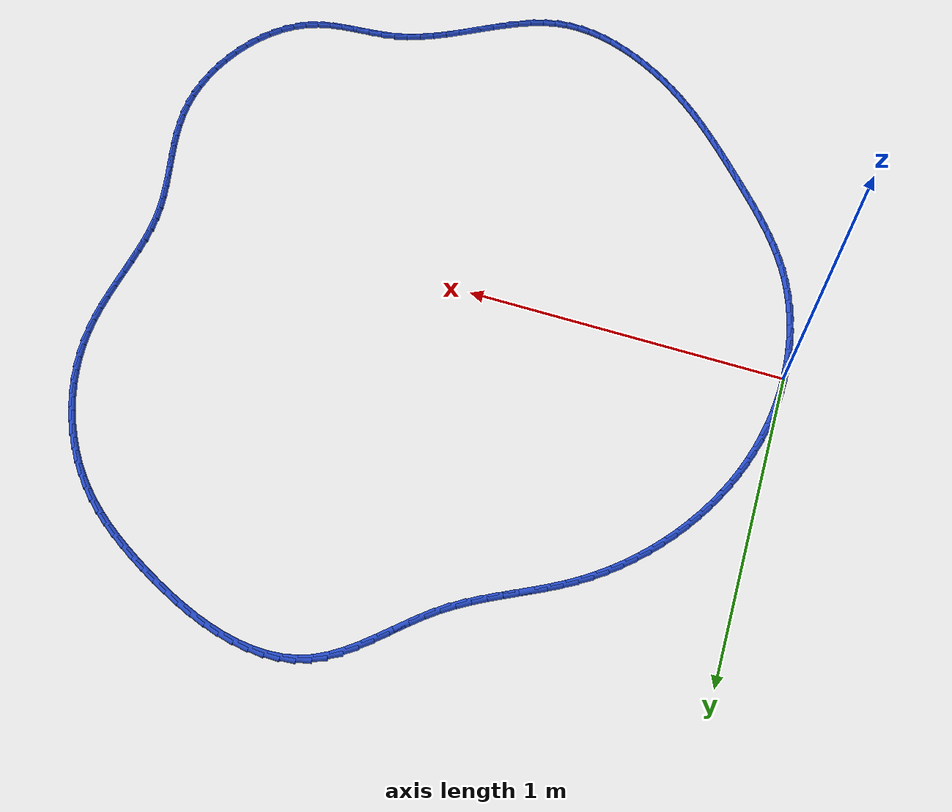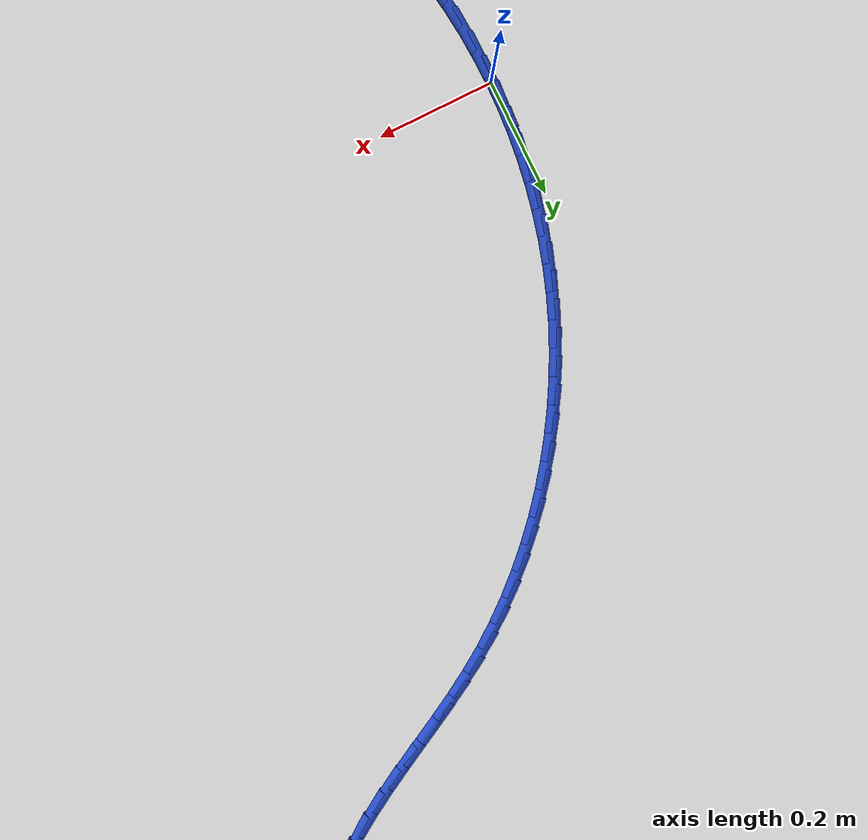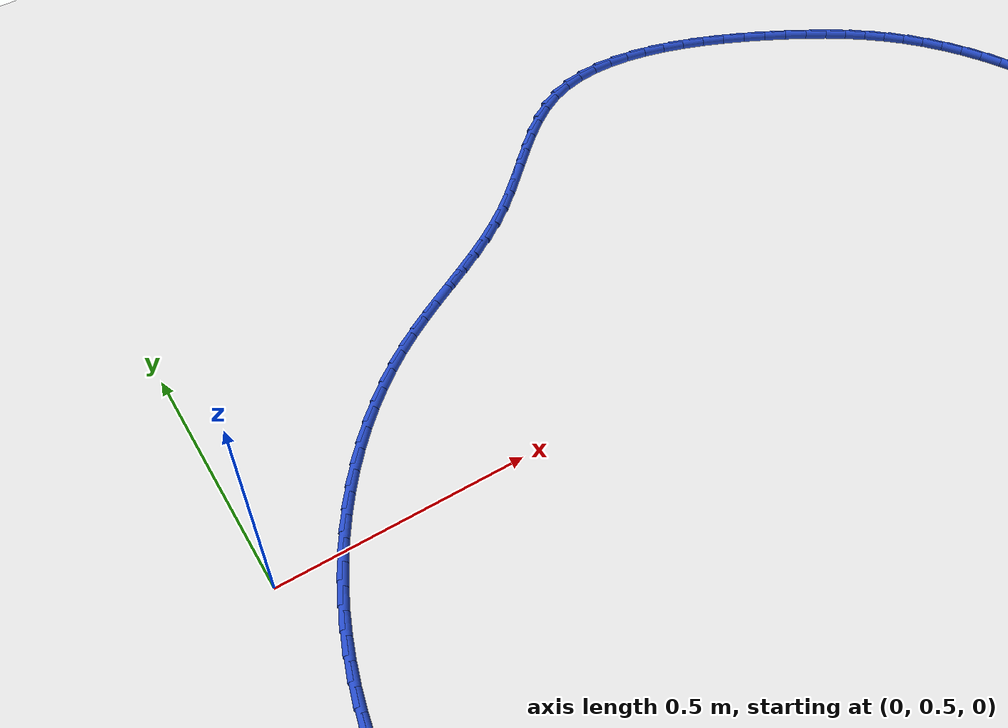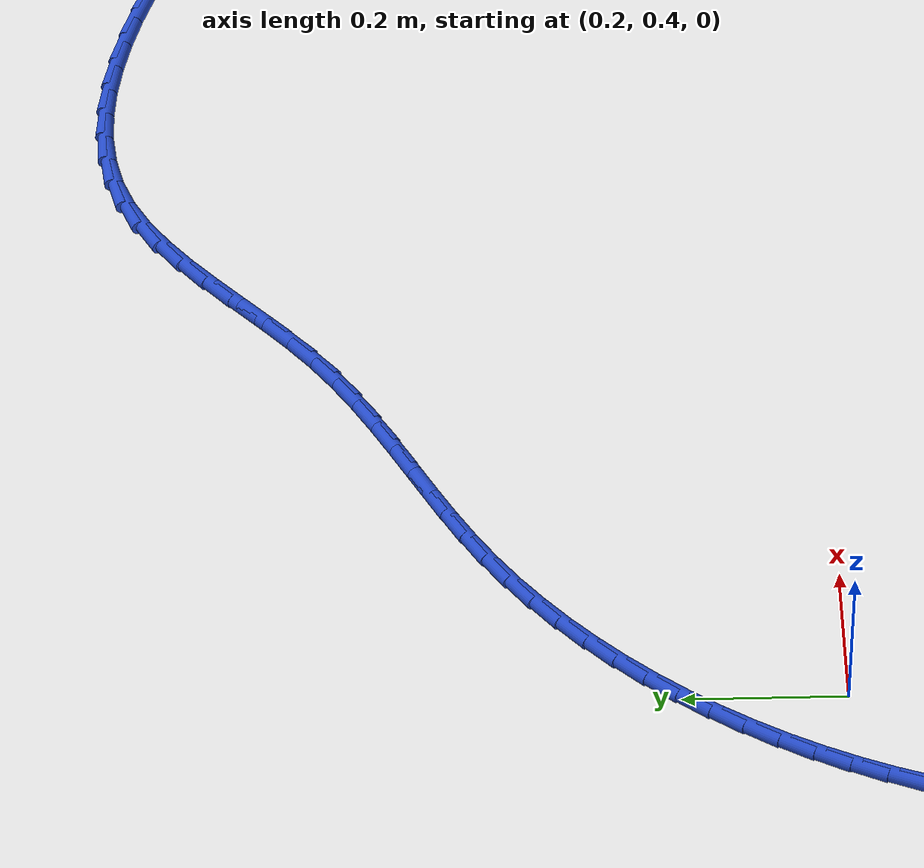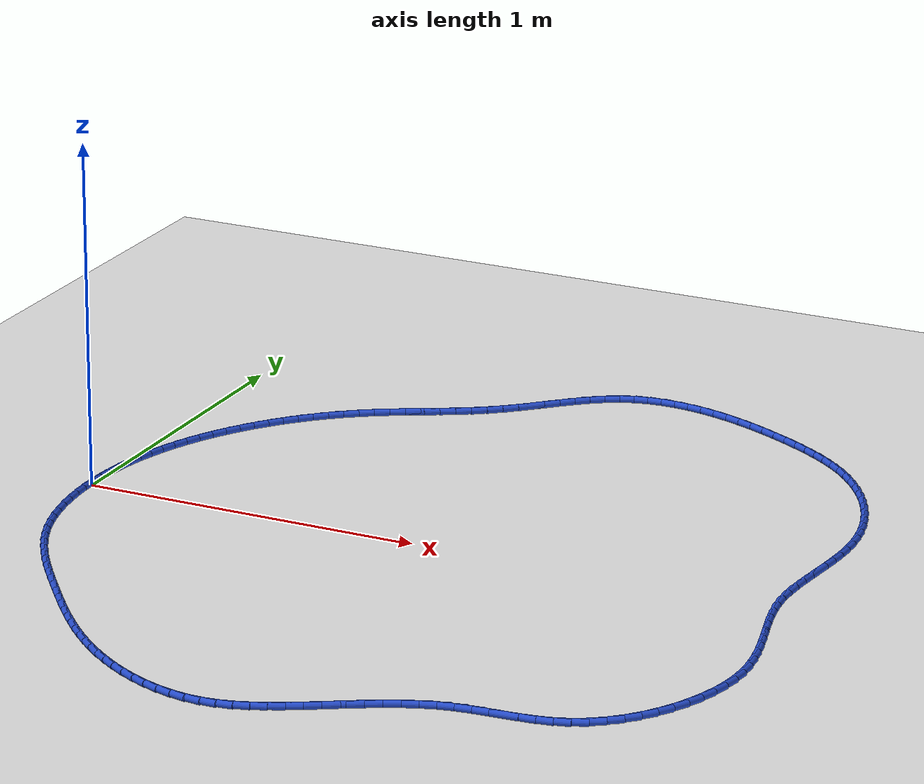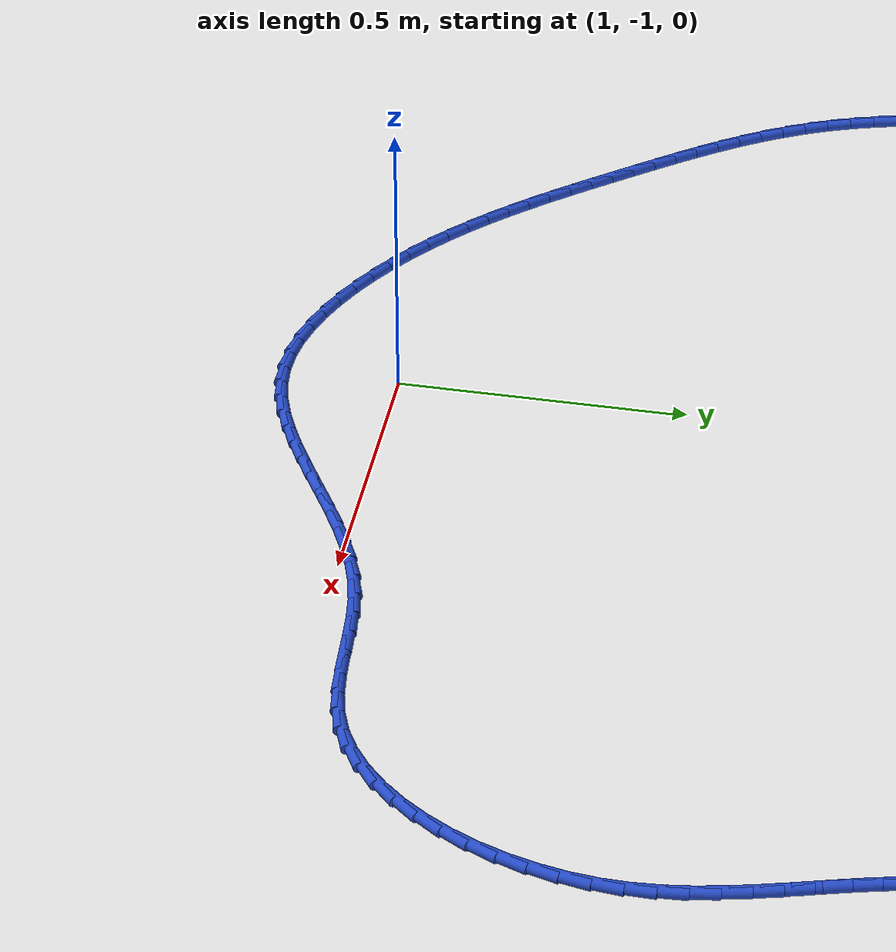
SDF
<sdf version="1.6">
 <world name="default">
  <light name="sun" type="directional">
   <pose>0 0 10 0 -0 0</pose>
   <diffuse>0.8 0.8 0.8 1</diffuse>
   <specular>0.2 0.2 0.2 1</specular>
   <attenuation>
    <range>1000</range>
    <constant>0.9</constant>
    <linear>0.01</linear>
    <quadratic>0.001</quadratic>
   </attenuation>
   <direction>-0.5 0.1 -0.9</direction>
  </light>
  <model name="ground_plane">
   <static>1</static>
   <link name="link">
    <collision name="collision">
     <geometry><plane><normal>0 0 1</normal><size>100 100</size></plane></geometry>
     <surface><friction><ode><mu>100</mu><mu2>50</mu2></ode></friction></surface>
    </collision>
    <visual name="visual">
     <cast_shadows>0</cast_shadows>
     <geometry><plane><normal>0 0 1</normal><size>100 100</size></plane></geometry>
     <material>
      <script><uri>file://media/materials/scripts/gazebo.material</uri><name>Gazebo/WhiteGlow</name></script>
     </material>
    </visual>
   </link>
  </model>
  <gravity>0 0 -9.8</gravity>
  <magnetic_field>6e-06 2.3e-05 -4.2e-05</magnetic_field>
  <atmosphere type="adiabatic"/>
  <physics name="default_physics" default="0" type="ode">
   <max_step_size>0.001</max_step_size>
   <real_time_factor>1</real_time_factor>
   <real_time_update_rate>1000</real_time_update_rate>
  </physics>
  <scene><ambient>0.4 0.4 0.4 1</ambient><background>0.7 0.7 0.7 1</background><shadows>1</shadows></scene>
  <spherical_coordinates>
   <surface_model>EARTH_WGS84</surface_model>
   <latitude_deg>0</latitude_deg>
   <longitude_deg>0</longitude_deg>
   <elevation>0</elevation>
   <heading_deg>0</heading_deg>
  </spherical_coordinates>
  <model name="line">
   <link name="link_0">
    <pose>2.7755575615628914e-17 -1.3877787807814457e-17 0.01 0 1.57 1.5438039051818868</pose>
    <collision name="collision">
     <geometry><cylinder><radius>0.01</radius><length>0.08</length></cylinder></geometry>
    </collision>
    <visual name="visual">
     <material>
      <script><name>Gazebo/Blue</name><uri>file://media/materials/scripts/gazebo.material</uri></script>
     </material>
     <geometry><cylinder><radius>0.01</radius><length>0.08</length></cylinder></geometry>
    </visual>
   </link>
   <link name="link_1">
    <pose>0.0012274226117992713 0.045461815861796415 0.01 0 1.57 1.5002485109680428</pose>
    <collision name="collision">
     <geometry><cylinder><radius>0.01</radius><length>0.08</length></cylinder></geometry>
    </collision>
    <visual name="visual">
     <material>
      <script><name>Gazebo/Blue</name><uri>file://media/materials/scripts/gazebo.material</uri></script>
     </material>
     <geometry><cylinder><radius>0.01</radius><length>0.08</length></cylinder></geometry>
    </visual>
   </link>
   <link name="link_2">
    <pose>0.004426673905857419 0.09073525123194078 0.01 0 1.57 1.456372147194954</pose>
    <collision name="collision">
     <geometry><cylinder><radius>0.01</radius><length>0.08</length></cylinder></geometry>
    </collision>
    <visual name="visual">
     <material>
      <script><name>Gazebo/Blue</name><uri>file://media/materials/scripts/gazebo.material</uri></script>
     </material>
     <geometry><cylinder><radius>0.01</radius><length>0.08</length></cylinder></geometry>
    </visual>
   </link>
   <link name="link_3">
    <pose>0.00960134744828331 0.13576131135203842 0.01 0 1.57 1.4121729207926326</pose>
    <collision name="collision">
     <geometry><cylinder><radius>0.01</radius><length>0.08</length></cylinder></geometry>
    </collision>
    <visual name="visual">
     <material>
      <script><name>Gazebo/Blue</name><uri>file://media/materials/scripts/gazebo.material</uri></script>
     </material>
     <geometry><cylinder><radius>0.01</radius><length>0.08</length></cylinder></geometry>
    </visual>
   </link>
   <link name="link_4">
    <pose>0.016755036805185752 0.18048100146369445 0.01 0 1.57 1.367653221788567</pose>
    <collision name="collision">
     <geometry><cylinder><radius>0.01</radius><length>0.08</length></cylinder></geometry>
    </collision>
    <visual name="visual">
     <material>
      <script><name>Gazebo/Blue</name><uri>file://media/materials/scripts/gazebo.material</uri></script>
     </material>
     <geometry><cylinder><radius>0.01</radius><length>0.08</length></cylinder></geometry>
    </visual>
   </link>
   <link name="link_5">
    <pose>0.02589133554267359 0.22483532680851429 0.01 0 1.57 1.322820274719058</pose>
    <collision name="collision">
     <geometry><cylinder><radius>0.01</radius><length>0.08</length></cylinder></geometry>
    </collision>
    <visual name="visual">
     <material>
      <script><name>Gazebo/Blue</name><uri>file://media/materials/scripts/gazebo.material</uri></script>
     </material>
     <geometry><cylinder><radius>0.01</radius><length>0.08</length></cylinder></geometry>
    </visual>
   </link>
   <link name="link_6">
    <pose>0.03701383722685566 0.26876529262810317 0.01 0 1.57 1.2776866372692732</pose>
    <collision name="collision">
     <geometry><cylinder><radius>0.01</radius><length>0.08</length></cylinder></geometry>
    </collision>
    <visual name="visual">
     <material>
      <script><name>Gazebo/Blue</name><uri>file://media/materials/scripts/gazebo.material</uri></script>
     </material>
     <geometry><cylinder><radius>0.01</radius><length>0.08</length></cylinder></geometry>
    </visual>
   </link>
   <link name="link_7">
    <pose>0.05012613542384077 0.31221190416406625 0.01 0 1.57 1.232270625870829</pose>
    <collision name="collision">
     <geometry><cylinder><radius>0.01</radius><length>0.08</length></cylinder></geometry>
    </collision>
    <visual name="visual">
     <material>
      <script><name>Gazebo/Blue</name><uri>file://media/materials/scripts/gazebo.material</uri></script>
     </material>
     <geometry><cylinder><radius>0.01</radius><length>0.08</length></cylinder></geometry>
    </visual>
   </link>
   <link name="link_8">
    <pose>0.06523182369973775 0.35511616665800894 0.01 0 1.57 1.186603532275354</pose>
    <collision name="collision">
     <geometry><cylinder><radius>0.01</radius><length>0.08</length></cylinder></geometry>
    </collision>
    <visual name="visual">
     <material>
      <script><name>Gazebo/Blue</name><uri>file://media/materials/scripts/gazebo.material</uri></script>
     </material>
     <geometry><cylinder><radius>0.01</radius><length>0.08</length></cylinder></geometry>
    </visual>
   </link>
   <link name="link_9">
    <pose>0.08233400079786048 0.3974186996037792 0.01 0 1.57 1.1410511294377066</pose>
    <collision name="collision">
     <geometry><cylinder><radius>0.01</radius><length>0.08</length></cylinder></geometry>
    </collision>
    <visual name="visual">
     <material>
      <script><name>Gazebo/Blue</name><uri>file://media/materials/scripts/gazebo.material</uri></script>
     </material>
     <geometry><cylinder><radius>0.01</radius><length>0.08</length></cylinder></geometry>
    </visual>
   </link>
   <link name="link_10">
    <pose>0.10140935679296745 0.43903953515613786 0.01 0 1.57 1.0960086770704474</pose>
    <collision name="collision">
     <geometry><cylinder><radius>0.01</radius><length>0.08</length></cylinder></geometry>
    </collision>
    <visual name="visual">
     <material>
      <script><name>Gazebo/Blue</name><uri>file://media/materials/scripts/gazebo.material</uri></script>
     </material>
     <geometry><cylinder><radius>0.01</radius><length>0.08</length></cylinder></geometry>
    </visual>
   </link>
   <link name="link_11">
    <pose>0.12239543092023891 0.47986818474865683 0.01 0 1.57 1.0513154567760972</pose>
    <collision name="collision">
     <geometry><cylinder><radius>0.01</radius><length>0.08</length></cylinder></geometry>
    </collision>
    <visual name="visual">
     <material>
      <script><name>Gazebo/Blue</name><uri>file://media/materials/scripts/gazebo.material</uri></script>
     </material>
     <geometry><cylinder><radius>0.01</radius><length>0.08</length></cylinder></geometry>
    </visual>
   </link>
   <link name="link_12">
    <pose>0.14522659465992305 0.5197916903361917 0.01 0 1.57 1.0067676363513318</pose>
    <collision name="collision">
     <geometry><cylinder><radius>0.01</radius><length>0.08</length></cylinder></geometry>
    </collision>
    <visual name="visual">
     <material>
      <script><name>Gazebo/Blue</name><uri>file://media/materials/scripts/gazebo.material</uri></script>
     </material>
     <geometry><cylinder><radius>0.01</radius><length>0.08</length></cylinder></geometry>
    </visual>
   </link>
   <link name="link_13">
    <pose>0.16983721949226793 0.5586970938735976 0.01 0 1.57 0.9621625291410923</pose>
    <collision name="collision">
     <geometry><cylinder><radius>0.01</radius><length>0.08</length></cylinder></geometry>
    </collision>
    <visual name="visual">
     <material>
      <script><name>Gazebo/Blue</name><uri>file://media/materials/scripts/gazebo.material</uri></script>
     </material>
     <geometry><cylinder><radius>0.01</radius><length>0.08</length></cylinder></geometry>
    </visual>
   </link>
   <link name="link_14">
    <pose>0.19616167689752204 0.5964714373157305 0.01 0 1.57 0.9172986936262948</pose>
    <collision name="collision">
     <geometry><cylinder><radius>0.01</radius><length>0.08</length></cylinder></geometry>
    </collision>
    <visual name="visual">
     <material>
      <script><name>Gazebo/Blue</name><uri>file://media/materials/scripts/gazebo.material</uri></script>
     </material>
     <geometry><cylinder><radius>0.01</radius><length>0.08</length></cylinder></geometry>
    </visual>
   </link>
   <link name="link_15">
    <pose>0.22413433835593333 0.6330017626174453 0.01 0 1.57 0.8719761058308376</pose>
    <collision name="collision">
     <geometry><cylinder><radius>0.01</radius><length>0.08</length></cylinder></geometry>
    </collision>
    <visual name="visual">
     <material>
      <script><name>Gazebo/Blue</name><uri>file://media/materials/scripts/gazebo.material</uri></script>
     </material>
     <geometry><cylinder><radius>0.01</radius><length>0.08</length></cylinder></geometry>
    </visual>
   </link>
   <link name="link_16">
    <pose>0.25368957534775016 0.6681751117335978 0.01 0 1.57 0.8259965544912151</pose>
    <collision name="collision">
     <geometry><cylinder><radius>0.01</radius><length>0.08</length></cylinder></geometry>
    </collision>
    <visual name="visual">
     <material>
      <script><name>Gazebo/Blue</name><uri>file://media/materials/scripts/gazebo.material</uri></script>
     </material>
     <geometry><cylinder><radius>0.01</radius><length>0.08</length></cylinder></geometry>
    </visual>
   </link>
   <link name="link_17">
    <pose>0.28476175935322073 0.7018785266190436 0.01 0 1.57 0.7791644137322374</pose>
    <collision name="collision">
     <geometry><cylinder><radius>0.01</radius><length>0.08</length></cylinder></geometry>
    </collision>
    <visual name="visual">
     <material>
      <script><name>Gazebo/Blue</name><uri>file://media/materials/scripts/gazebo.material</uri></script>
     </material>
     <geometry><cylinder><radius>0.01</radius><length>0.08</length></cylinder></geometry>
    </visual>
   </link>
   <link name="link_18">
    <pose>0.31728526185259315 0.7339990492286378 0.01 0 1.57 0.7312879565658935</pose>
    <collision name="collision">
     <geometry><cylinder><radius>0.01</radius><length>0.08</length></cylinder></geometry>
    </collision>
    <visual name="visual">
     <material>
      <script><name>Gazebo/Blue</name><uri>file://media/materials/scripts/gazebo.material</uri></script>
     </material>
     <geometry><cylinder><radius>0.01</radius><length>0.08</length></cylinder></geometry>
    </visual>
   </link>
   <link name="link_19">
    <pose>0.3511944543261158 0.764423721517236 0.01 0 1.57 0.682181381445582</pose>
    <collision name="collision">
     <geometry><cylinder><radius>0.01</radius><length>0.08</length></cylinder></geometry>
    </collision>
    <visual name="visual">
     <material>
      <script><name>Gazebo/Blue</name><uri>file://media/materials/scripts/gazebo.material</uri></script>
     </material>
     <geometry><cylinder><radius>0.01</radius><length>0.08</length></cylinder></geometry>
    </visual>
   </link>
   <link name="link_20">
    <pose>0.38642370825403666 0.7930395854396936 0.01 0 1.57 0.6316677280078654</pose>
    <collision name="collision">
     <geometry><cylinder><radius>0.01</radius><length>0.08</length></cylinder></geometry>
    </collision>
    <visual name="visual">
     <material>
      <script><name>Gazebo/Blue</name><uri>file://media/materials/scripts/gazebo.material</uri></script>
     </material>
     <geometry><cylinder><radius>0.01</radius><length>0.08</length></cylinder></geometry>
    </visual>
   </link>
   <link name="link_21">
    <pose>0.4229073951166042 0.8197336829508661 0.01 0 1.57 0.5801251381507768</pose>
    <collision name="collision">
     <geometry><cylinder><radius>0.01</radius><length>0.08</length></cylinder></geometry>
    </collision>
    <visual name="visual">
     <material>
      <script><name>Gazebo/Blue</name><uri>file://media/materials/scripts/gazebo.material</uri></script>
     </material>
     <geometry><cylinder><radius>0.01</radius><length>0.08</length></cylinder></geometry>
    </visual>
   </link>
   <link name="link_22">
    <pose>0.4605715760902958 0.844416802883559 0.01 0 1.57 0.5359944190135996</pose>
    <collision name="collision">
     <geometry><cylinder><radius>0.01</radius><length>0.08</length></cylinder></geometry>
    </collision>
    <visual name="visual">
     <material>
      <script><name>Gazebo/Blue</name><uri>file://media/materials/scripts/gazebo.material</uri></script>
     </material>
     <geometry><cylinder><radius>0.01</radius><length>0.08</length></cylinder></geometry>
    </visual>
   </link>
   <link name="link_23">
    <pose>0.49921286204348236 0.8673696412066021 0.01 0 1.57 0.5062288535295115</pose>
    <collision name="collision">
     <geometry><cylinder><radius>0.01</radius><length>0.08</length></cylinder></geometry>
    </collision>
    <visual name="visual">
     <material>
      <script><name>Gazebo/Blue</name><uri>file://media/materials/scripts/gazebo.material</uri></script>
     </material>
     <geometry><cylinder><radius>0.01</radius><length>0.08</length></cylinder></geometry>
    </visual>
   </link>
   <link name="link_24">
    <pose>0.5385255362949087 0.8891652971389342 0.01 0 1.57 0.4911193388827673</pose>
    <collision name="collision">
     <geometry><cylinder><radius>0.01</radius><length>0.08</length></cylinder></geometry>
    </collision>
    <visual name="visual">
     <material>
      <script><name>Gazebo/Blue</name><uri>file://media/materials/scripts/gazebo.material</uri></script>
     </material>
     <geometry><cylinder><radius>0.01</radius><length>0.08</length></cylinder></geometry>
    </visual>
   </link>
   <link name="link_25">
    <pose>0.5782010905877437 0.910384846888824 0.01 0 1.57 0.4906473573979358</pose>
    <collision name="collision">
     <geometry><cylinder><radius>0.01</radius><length>0.08</length></cylinder></geometry>
    </collision>
    <visual name="visual">
     <material>
      <script><name>Gazebo/Blue</name><uri>file://media/materials/scripts/gazebo.material</uri></script>
     </material>
     <geometry><cylinder><radius>0.01</radius><length>0.08</length></cylinder></geometry>
    </visual>
   </link>
   <link name="link_26">
    <pose>0.6179310166651563 0.9316093666645406 0.01 0 1.57 0.5047643014628631</pose>
    <collision name="collision">
     <geometry><cylinder><radius>0.01</radius><length>0.08</length></cylinder></geometry>
    </collision>
    <visual name="visual">
     <material>
      <script><name>Gazebo/Blue</name><uri>file://media/materials/scripts/gazebo.material</uri></script>
     </material>
     <geometry><cylinder><radius>0.01</radius><length>0.08</length></cylinder></geometry>
    </visual>
   </link>
   <link name="link_27">
    <pose>0.6574068062703151 0.9534199326743527 0.01 0 1.57 0.5333949445838942</pose>
    <collision name="collision">
     <geometry><cylinder><radius>0.01</radius><length>0.08</length></cylinder></geometry>
    </collision>
    <visual name="visual">
     <material>
      <script><name>Gazebo/Blue</name><uri>file://media/materials/scripts/gazebo.material</uri></script>
     </material>
     <geometry><cylinder><radius>0.01</radius><length>0.08</length></cylinder></geometry>
    </visual>
   </link>
   <link name="link_28">
    <pose>0.6963199511463887 0.9763976211265286 0.01 0 1.57 0.5763492082743317</pose>
    <collision name="collision">
     <geometry><cylinder><radius>0.01</radius><length>0.08</length></cylinder></geometry>
    </collision>
    <visual name="visual">
     <material>
      <script><name>Gazebo/Blue</name><uri>file://media/materials/scripts/gazebo.material</uri></script>
     </material>
     <geometry><cylinder><radius>0.01</radius><length>0.08</length></cylinder></geometry>
    </visual>
   </link>
   <link name="link_29">
    <pose>0.734361943036546 1.0011235082293375 0.01 0 1.57 0.6331506874559334</pose>
    <collision name="collision">
     <geometry><cylinder><radius>0.01</radius><length>0.08</length></cylinder></geometry>
    </collision>
    <visual name="visual">
     <material>
      <script><name>Gazebo/Blue</name><uri>file://media/materials/scripts/gazebo.material</uri></script>
     </material>
     <geometry><cylinder><radius>0.01</radius><length>0.08</length></cylinder></geometry>
    </visual>
   </link>
   <link name="link_30">
    <pose>0.7712242736839553 1.0281786701910478 0.01 0 1.57 0.6967573670954323</pose>
    <collision name="collision">
     <geometry><cylinder><radius>0.01</radius><length>0.08</length></cylinder></geometry>
    </collision>
    <visual name="visual">
     <material>
      <script><name>Gazebo/Blue</name><uri>file://media/materials/scripts/gazebo.material</uri></script>
     </material>
     <geometry><cylinder><radius>0.01</radius><length>0.08</length></cylinder></geometry>
    </visual>
   </link>
   <link name="link_31">
    <pose>0.8067190815543362 1.0578793177478278 0.01 0 1.57 0.7418646541711746</pose>
    <collision name="collision">
     <geometry><cylinder><radius>0.01</radius><length>0.08</length></cylinder></geometry>
    </collision>
    <visual name="visual">
     <material>
      <script><name>Gazebo/Blue</name><uri>file://media/materials/scripts/gazebo.material</uri></script>
     </material>
     <geometry><cylinder><radius>0.01</radius><length>0.08</length></cylinder></geometry>
    </visual>
   </link>
   <link name="link_32">
    <pose>0.8411586392800531 1.0894436767974454 0.01 0 1.57 0.7632778604231394</pose>
    <collision name="collision">
     <geometry><cylinder><radius>0.01</radius><length>0.08</length></cylinder></geometry>
    </collision>
    <visual name="visual">
     <material>
      <script><name>Gazebo/Blue</name><uri>file://media/materials/scripts/gazebo.material</uri></script>
     </material>
     <geometry><cylinder><radius>0.01</radius><length>0.08</length></cylinder></geometry>
    </visual>
   </link>
   <link name="link_33">
    <pose>0.8749847981929068 1.121805498676944 0.01 0 1.57 0.7616515718498925</pose>
    <collision name="collision">
     <geometry><cylinder><radius>0.01</radius><length>0.08</length></cylinder></geometry>
    </collision>
    <visual name="visual">
     <material>
      <script><name>Gazebo/Blue</name><uri>file://media/materials/scripts/gazebo.material</uri></script>
     </material>
     <geometry><cylinder><radius>0.01</radius><length>0.08</length></cylinder></geometry>
    </visual>
   </link>
   <link name="link_34">
    <pose>0.9086394098356655 1.153898534260214 0.01 0 1.57 0.7364766078494152</pose>
    <collision name="collision">
     <geometry><cylinder><radius>0.01</radius><length>0.08</length></cylinder></geometry>
    </collision>
    <visual name="visual">
     <material>
      <script><name>Gazebo/Blue</name><uri>file://media/materials/scripts/gazebo.material</uri></script>
     </material>
     <geometry><cylinder><radius>0.01</radius><length>0.08</length></cylinder></geometry>
    </visual>
   </link>
   <link name="link_35">
    <pose>0.9425643257510968 1.1846565344211464 0.01 0 1.57 0.6860285060387574</pose>
    <collision name="collision">
     <geometry><cylinder><radius>0.01</radius><length>0.08</length></cylinder></geometry>
    </collision>
    <visual name="visual">
     <material>
      <script><name>Gazebo/Blue</name><uri>file://media/materials/scripts/gazebo.material</uri></script>
     </material>
     <geometry><cylinder><radius>0.01</radius><length>0.08</length></cylinder></geometry>
    </visual>
   </link>
   <link name="link_36">
    <pose>0.9772013974819684 1.2130132500336317 0.01 0 1.57 0.6076332740044071</pose>
    <collision name="collision">
     <geometry><cylinder><radius>0.01</radius><length>0.08</length></cylinder></geometry>
    </collision>
    <visual name="visual">
     <material>
      <script><name>Gazebo/Blue</name><uri>file://media/materials/scripts/gazebo.material</uri></script>
     </material>
     <geometry><cylinder><radius>0.01</radius><length>0.08</length></cylinder></geometry>
    </visual>
   </link>
   <link name="link_37">
    <pose>1.012992476571048 1.2379024319715608 0.01 0 1.57 0.49857385690341627</pose>
    <collision name="collision">
     <geometry><cylinder><radius>0.01</radius><length>0.08</length></cylinder></geometry>
    </collision>
    <visual name="visual">
     <material>
      <script><name>Gazebo/Blue</name><uri>file://media/materials/scripts/gazebo.material</uri></script>
     </material>
     <geometry><cylinder><radius>0.01</radius><length>0.08</length></cylinder></geometry>
    </visual>
   </link>
   <link name="link_38">
    <pose>1.0503794145611038 1.2582578311088246 0.01 0 1.57 0.3615146965251408</pose>
    <collision name="collision">
     <geometry><cylinder><radius>0.01</radius><length>0.08</length></cylinder></geometry>
    </collision>
    <visual name="visual">
     <material>
      <script><name>Gazebo/Blue</name><uri>file://media/materials/scripts/gazebo.material</uri></script>
     </material>
     <geometry><cylinder><radius>0.01</radius><length>0.08</length></cylinder></geometry>
    </visual>
   </link>
   <link name="link_39">
    <pose>1.089740830717486 1.2731416868704672 0.01 0 1.57 0.22454168957132323</pose>
    <collision name="collision">
     <geometry><cylinder><radius>0.01</radius><length>0.08</length></cylinder></geometry>
    </collision>
    <visual name="visual">
     <material>
      <script><name>Gazebo/Blue</name><uri>file://media/materials/scripts/gazebo.material</uri></script>
     </material>
     <geometry><cylinder><radius>0.01</radius><length>0.08</length></cylinder></geometry>
    </visual>
   </link>
   <link name="link_40">
    <pose>1.1309896061982043 1.282562622665678 0.01 0 1.57 0.1021054157653638</pose>
    <collision name="collision">
     <geometry><cylinder><radius>0.01</radius><length>0.08</length></cylinder></geometry>
    </collision>
    <visual name="visual">
     <material>
      <script><name>Gazebo/Blue</name><uri>file://media/materials/scripts/gazebo.material</uri></script>
     </material>
     <geometry><cylinder><radius>0.01</radius><length>0.08</length></cylinder></geometry>
    </visual>
   </link>
   <link name="link_41">
    <pose>1.1738304967151638 1.28695217466467 0.01 0 1.57 -0.004720008758100414</pose>
    <collision name="collision">
     <geometry><cylinder><radius>0.01</radius><length>0.08</length></cylinder></geometry>
    </collision>
    <visual name="visual">
     <material>
      <script><name>Gazebo/Blue</name><uri>file://media/materials/scripts/gazebo.material</uri></script>
     </material>
     <geometry><cylinder><radius>0.01</radius><length>0.08</length></cylinder></geometry>
    </visual>
   </link>
   <link name="link_42">
    <pose>1.2179672894650235 1.2867438470692596 0.01 0 1.57 -0.09657597802571115</pose>
    <collision name="collision">
     <geometry><cylinder><radius>0.01</radius><length>0.08</length></cylinder></geometry>
    </collision>
    <visual name="visual">
     <material>
      <script><name>Gazebo/Blue</name><uri>file://media/materials/scripts/gazebo.material</uri></script>
     </material>
     <geometry><cylinder><radius>0.01</radius><length>0.08</length></cylinder></geometry>
    </visual>
   </link>
   <link name="link_43">
    <pose>1.2631037716444435 1.2823711440812653 0.01 0 1.57 -0.1749719595927593</pose>
    <collision name="collision">
     <geometry><cylinder><radius>0.01</radius><length>0.08</length></cylinder></geometry>
    </collision>
    <visual name="visual">
     <material>
      <script><name>Gazebo/Blue</name><uri>file://media/materials/scripts/gazebo.material</uri></script>
     </material>
     <geometry><cylinder><radius>0.01</radius><length>0.08</length></cylinder></geometry>
    </visual>
   </link>
   <link name="link_44">
    <pose>1.3089437304500848 1.2742675699025054 0.01 0 1.57 -0.2417022427048707</pose>
    <collision name="collision">
     <geometry><cylinder><radius>0.01</radius><length>0.08</length></cylinder></geometry>
    </collision>
    <visual name="visual">
     <material>
      <script><name>Gazebo/Blue</name><uri>file://media/materials/scripts/gazebo.material</uri></script>
     </material>
     <geometry><cylinder><radius>0.01</radius><length>0.08</length></cylinder></geometry>
    </visual>
   </link>
   <link name="link_45">
    <pose>1.355190953078606 1.2628666287347972 0.01 0 1.57 -0.29851311467358155</pose>
    <collision name="collision">
     <geometry><cylinder><radius>0.01</radius><length>0.08</length></cylinder></geometry>
    </collision>
    <visual name="visual">
     <material>
      <script><name>Gazebo/Blue</name><uri>file://media/materials/scripts/gazebo.material</uri></script>
     </material>
     <geometry><cylinder><radius>0.01</radius><length>0.08</length></cylinder></geometry>
    </visual>
   </link>
   <link name="link_46">
    <pose>1.4015492267266678 1.2486018247799584 0.01 0 1.57 -0.3469514701376471</pose>
    <collision name="collision">
     <geometry><cylinder><radius>0.01</radius><length>0.08</length></cylinder></geometry>
    </collision>
    <visual name="visual">
     <material>
      <script><name>Gazebo/Blue</name><uri>file://media/materials/scripts/gazebo.material</uri></script>
     </material>
     <geometry><cylinder><radius>0.01</radius><length>0.08</length></cylinder></geometry>
    </visual>
   </link>
   <link name="link_47">
    <pose>1.4477223385909295 1.2319066622398078 0.01 0 1.57 -0.3883176417075081</pose>
    <collision name="collision">
     <geometry><cylinder><radius>0.01</radius><length>0.08</length></cylinder></geometry>
    </collision>
    <visual name="visual">
     <material>
      <script><name>Gazebo/Blue</name><uri>file://media/materials/scripts/gazebo.material</uri></script>
     </material>
     <geometry><cylinder><radius>0.01</radius><length>0.08</length></cylinder></geometry>
    </visual>
   </link>
   <link name="link_48">
    <pose>1.4934140758680519 1.2132146453161623 0.01 0 1.57 -0.4236682960750707</pose>
    <collision name="collision">
     <geometry><cylinder><radius>0.01</radius><length>0.08</length></cylinder></geometry>
    </collision>
    <visual name="visual">
     <material>
      <script><name>Gazebo/Blue</name><uri>file://media/materials/scripts/gazebo.material</uri></script>
     </material>
     <geometry><cylinder><radius>0.01</radius><length>0.08</length></cylinder></geometry>
    </visual>
   </link>
   <link name="link_49">
    <pose>1.538328225754694 1.1929592782108407 0.01 0 1.57 -0.45383804358030894</pose>
    <collision name="collision">
     <geometry><cylinder><radius>0.01</radius><length>0.08</length></cylinder></geometry>
    </collision>
    <visual name="visual">
     <material>
      <script><name>Gazebo/Blue</name><uri>file://media/materials/scripts/gazebo.material</uri></script>
     </material>
     <geometry><cylinder><radius>0.01</radius><length>0.08</length></cylinder></geometry>
    </visual>
   </link>
   <link name="link_50">
    <pose>1.5821685754475168 1.1715740651256612 0.01 0 1.57 -0.4796083093968417</pose>
    <collision name="collision">
     <geometry><cylinder><radius>0.01</radius><length>0.08</length></cylinder></geometry>
    </collision>
    <visual name="visual">
     <material>
      <script><name>Gazebo/Blue</name><uri>file://media/materials/scripts/gazebo.material</uri></script>
     </material>
     <geometry><cylinder><radius>0.01</radius><length>0.08</length></cylinder></geometry>
    </visual>
   </link>
   <link name="link_51">
    <pose>1.6246428211755533 1.14948265380952 0.01 0 1.57 -0.5059911623043839</pose>
    <collision name="collision">
     <geometry><cylinder><radius>0.01</radius><length>0.08</length></cylinder></geometry>
    </collision>
    <visual name="visual">
     <material>
      <script><name>Gazebo/Blue</name><uri>file://media/materials/scripts/gazebo.material</uri></script>
     </material>
     <geometry><cylinder><radius>0.01</radius><length>0.08</length></cylinder></geometry>
    </visual>
   </link>
   <link name="link_52">
    <pose>1.6655818672639306 1.1267980282249066 0.01 0 1.57 -0.5386048622359725</pose>
    <collision name="collision">
     <geometry><cylinder><radius>0.01</radius><length>0.08</length></cylinder></geometry>
    </collision>
    <visual name="visual">
     <material>
      <script><name>Gazebo/Blue</name><uri>file://media/materials/scripts/gazebo.material</uri></script>
     </material>
     <geometry><cylinder><radius>0.01</radius><length>0.08</length></cylinder></geometry>
    </visual>
   </link>
   <link name="link_53">
    <pose>1.7049617757692292 1.1032671635093199 0.01 0 1.57 -0.5778203242649008</pose>
    <collision name="collision">
     <geometry><cylinder><radius>0.01</radius><length>0.08</length></cylinder></geometry>
    </collision>
    <visual name="visual">
     <material>
      <script><name>Gazebo/Blue</name><uri>file://media/materials/scripts/gazebo.material</uri></script>
     </material>
     <geometry><cylinder><radius>0.01</radius><length>0.08</length></cylinder></geometry>
    </visual>
   </link>
   <link name="link_54">
    <pose>1.7427669447291079 1.0786160159912048 0.01 0 1.57 -0.6234917984341739</pose>
    <collision name="collision">
     <geometry><cylinder><radius>0.01</radius><length>0.08</length></cylinder></geometry>
    </collision>
    <visual name="visual">
     <material>
      <script><name>Gazebo/Blue</name><uri>file://media/materials/scripts/gazebo.material</uri></script>
     </material>
     <geometry><cylinder><radius>0.01</radius><length>0.08</length></cylinder></geometry>
    </visual>
   </link>
   <link name="link_55">
    <pose>1.7789817721812275 1.0525705419990066 0.01 0 1.57 -0.6752118293213302</pose>
    <collision name="collision">
     <geometry><cylinder><radius>0.01</radius><length>0.08</length></cylinder></geometry>
    </collision>
    <visual name="visual">
     <material>
      <script><name>Gazebo/Blue</name><uri>file://media/materials/scripts/gazebo.material</uri></script>
     </material>
     <geometry><cylinder><radius>0.01</radius><length>0.08</length></cylinder></geometry>
    </visual>
   </link>
   <link name="link_56">
    <pose>1.8135906561632495 1.0248566978611697 0.01 0 1.57 -0.7322730804000313</pose>
    <collision name="collision">
     <geometry><cylinder><radius>0.01</radius><length>0.08</length></cylinder></geometry>
    </collision>
    <visual name="visual">
     <material>
      <script><name>Gazebo/Blue</name><uri>file://media/materials/scripts/gazebo.material</uri></script>
     </material>
     <geometry><cylinder><radius>0.01</radius><length>0.08</length></cylinder></geometry>
    </visual>
   </link>
   <link name="link_57">
    <pose>1.8465779947128316 0.9952004399061394 0.01 0 1.57 -0.7935373932886136</pose>
    <collision name="collision">
     <geometry><cylinder><radius>0.01</radius><length>0.08</length></cylinder></geometry>
    </collision>
    <visual name="visual">
     <material>
      <script><name>Gazebo/Blue</name><uri>file://media/materials/scripts/gazebo.material</uri></script>
     </material>
     <geometry><cylinder><radius>0.01</radius><length>0.08</length></cylinder></geometry>
    </visual>
   </link>
   <link name="link_58">
    <pose>1.877925598969698 0.9633383460235726 0.01 0 1.57 -0.8553717081865992</pose>
    <collision name="collision">
     <geometry><cylinder><radius>0.01</radius><length>0.08</length></cylinder></geometry>
    </collision>
    <visual name="visual">
     <material>
      <script><name>Gazebo/Blue</name><uri>file://media/materials/scripts/gazebo.material</uri></script>
     </material>
     <geometry><cylinder><radius>0.01</radius><length>0.08</length></cylinder></geometry>
    </visual>
   </link>
   <link name="link_59">
    <pose>1.9075590341004098 0.9292379348132972 0.01 0 1.57 -0.9153683888444641</pose>
    <collision name="collision">
     <geometry><cylinder><radius>0.01</radius><length>0.08</length></cylinder></geometry>
    </collision>
    <visual name="visual">
     <material>
      <script><name>Gazebo/Blue</name><uri>file://media/materials/scripts/gazebo.material</uri></script>
     </material>
     <geometry><cylinder><radius>0.01</radius><length>0.08</length></cylinder></geometry>
    </visual>
   </link>
   <link name="link_60">
    <pose>1.9353493691079897 0.8930904810305077 0.01 0 1.57 -0.9739775218266095</pose>
    <collision name="collision">
     <geometry><cylinder><radius>0.01</radius><length>0.08</length></cylinder></geometry>
    </collision>
    <visual name="visual">
     <material>
      <script><name>Gazebo/Blue</name><uri>file://media/materials/scripts/gazebo.material</uri></script>
     </material>
     <geometry><cylinder><radius>0.01</radius><length>0.08</length></cylinder></geometry>
    </visual>
   </link>
   <link name="link_61">
    <pose>1.961165436169029 0.8550964436307218 0.01 0 1.57 -1.031740676865908</pose>
    <collision name="collision">
     <geometry><cylinder><radius>0.01</radius><length>0.08</length></cylinder></geometry>
    </collision>
    <visual name="visual">
     <material>
      <script><name>Gazebo/Blue</name><uri>file://media/materials/scripts/gazebo.material</uri></script>
     </material>
     <geometry><cylinder><radius>0.01</radius><length>0.08</length></cylinder></geometry>
    </visual>
   </link>
   <link name="link_62">
    <pose>1.9848760674601162 0.8154562815694585 0.01 0 1.57 -1.0891834034690284</pose>
    <collision name="collision">
     <geometry><cylinder><radius>0.01</radius><length>0.08</length></cylinder></geometry>
    </collision>
    <visual name="visual">
     <material>
      <script><name>Gazebo/Blue</name><uri>file://media/materials/scripts/gazebo.material</uri></script>
     </material>
     <geometry><cylinder><radius>0.01</radius><length>0.08</length></cylinder></geometry>
    </visual>
   </link>
   <link name="link_63">
    <pose>2.0063500951578437 0.7743704538022356 0.01 0 1.57 -1.1468174837628655</pose>
    <collision name="collision">
     <geometry><cylinder><radius>0.01</radius><length>0.08</length></cylinder></geometry>
    </collision>
    <visual name="visual">
     <material>
      <script><name>Gazebo/Blue</name><uri>file://media/materials/scripts/gazebo.material</uri></script>
     </material>
     <geometry><cylinder><radius>0.01</radius><length>0.08</length></cylinder></geometry>
    </visual>
   </link>
   <link name="link_64">
    <pose>2.0254563514387995 0.7320394192845711 0.01 0 1.57 -1.2051432167218241</pose>
    <collision name="collision">
     <geometry><cylinder><radius>0.01</radius><length>0.08</length></cylinder></geometry>
    </collision>
    <visual name="visual">
     <material>
      <script><name>Gazebo/Blue</name><uri>file://media/materials/scripts/gazebo.material</uri></script>
     </material>
     <geometry><cylinder><radius>0.01</radius><length>0.08</length></cylinder></geometry>
    </visual>
   </link>
   <link name="link_65">
    <pose>2.042063668479575 0.6886636369719832 0.01 0 1.57 -1.2646506255794638</pose>
    <collision name="collision">
     <geometry><cylinder><radius>0.01</radius><length>0.08</length></cylinder></geometry>
    </collision>
    <visual name="visual">
     <material>
      <script><name>Gazebo/Blue</name><uri>file://media/materials/scripts/gazebo.material</uri></script>
     </material>
     <geometry><cylinder><radius>0.01</radius><length>0.08</length></cylinder></geometry>
    </visual>
   </link>
   <link name="link_66">
    <pose>2.056040878456761 0.6444435658199897 0.01 0 1.57 -1.3258185063482864</pose>
    <collision name="collision">
     <geometry><cylinder><radius>0.01</radius><length>0.08</length></cylinder></geometry>
    </collision>
    <visual name="visual">
     <material>
      <script><name>Gazebo/Blue</name><uri>file://media/materials/scripts/gazebo.material</uri></script>
     </material>
     <geometry><cylinder><radius>0.01</radius><length>0.08</length></cylinder></geometry>
    </visual>
   </link>
   <link name="link_67">
    <pose>2.067256813546946 0.5995796647841094 0.01 0 1.57 -1.3891101634029779</pose>
    <collision name="collision">
     <geometry><cylinder><radius>0.01</radius><length>0.08</length></cylinder></geometry>
    </collision>
    <visual name="visual">
     <material>
      <script><name>Gazebo/Blue</name><uri>file://media/materials/scripts/gazebo.material</uri></script>
     </material>
     <geometry><cylinder><radius>0.01</radius><length>0.08</length></cylinder></geometry>
    </visual>
   </link>
   <link name="link_68">
    <pose>2.0755803059267213 0.5542723928198596 0.01 0 1.57 -1.4549645708984056</pose>
    <collision name="collision">
     <geometry><cylinder><radius>0.01</radius><length>0.08</length></cylinder></geometry>
    </collision>
    <visual name="visual">
     <material>
      <script><name>Gazebo/Blue</name><uri>file://media/materials/scripts/gazebo.material</uri></script>
     </material>
     <geometry><cylinder><radius>0.01</radius><length>0.08</length></cylinder></geometry>
    </visual>
   </link>
   <link name="link_69">
    <pose>2.0808801877726766 0.5087222088827593 0.01 0 1.57 -1.5218819057155206</pose>
    <collision name="collision">
     <geometry><cylinder><radius>0.01</radius><length>0.08</length></cylinder></geometry>
    </collision>
    <visual name="visual">
     <material>
      <script><name>Gazebo/Blue</name><uri>file://media/materials/scripts/gazebo.material</uri></script>
     </material>
     <geometry><cylinder><radius>0.01</radius><length>0.08</length></cylinder></geometry>
    </visual>
   </link>
   <link name="link_70">
    <pose>2.0831130327107257 0.4631106321511463 0.01 0 1.57 1.5624668615987558</pose>
    <collision name="collision">
     <geometry><cylinder><radius>0.01</radius><length>0.08</length></cylinder></geometry>
    </collision>
    <visual name="visual">
     <material>
      <script><name>Gazebo/Blue</name><uri>file://media/materials/scripts/gazebo.material</uri></script>
     </material>
     <geometry><cylinder><radius>0.01</radius><length>0.08</length></cylinder></geometry>
    </visual>
   </link>
   <link name="link_71">
    <pose>2.0827332094438664 0.41751172828037597 0.01 0 1.57 1.5189704209391668</pose>
    <collision name="collision">
     <geometry><cylinder><radius>0.01</radius><length>0.08</length></cylinder></geometry>
    </collision>
    <visual name="visual">
     <material>
      <script><name>Gazebo/Blue</name><uri>file://media/materials/scripts/gazebo.material</uri></script>
     </material>
     <geometry><cylinder><radius>0.01</radius><length>0.08</length></cylinder></geometry>
    </visual>
   </link>
   <link name="link_72">
    <pose>2.080370422944099 0.37196171502276654 0.01 0 1.57 1.4892476107265884</pose>
    <collision name="collision">
     <geometry><cylinder><radius>0.01</radius><length>0.08</length></cylinder></geometry>
    </collision>
    <visual name="visual">
     <material>
      <script><name>Gazebo/Blue</name><uri>file://media/materials/scripts/gazebo.material</uri></script>
     </material>
     <geometry><cylinder><radius>0.01</radius><length>0.08</length></cylinder></geometry>
    </visual>
   </link>
   <link name="link_73">
    <pose>2.076654574182375 0.32649676782250664 0.01 0 1.57 1.4732103422160938</pose>
    <collision name="collision">
     <geometry><cylinder><radius>0.01</radius><length>0.08</length></cylinder></geometry>
    </collision>
    <visual name="visual">
     <material>
      <script><name>Gazebo/Blue</name><uri>file://media/materials/scripts/gazebo.material</uri></script>
     </material>
     <geometry><cylinder><radius>0.01</radius><length>0.08</length></cylinder></geometry>
    </visual>
   </link>
   <link name="link_74">
    <pose>2.0722155641296447 0.28115306212378616 0.01 0 1.57 1.4708287776821645</pose>
    <collision name="collision">
     <geometry><cylinder><radius>0.01</radius><length>0.08</length></cylinder></geometry>
    </collision>
    <visual name="visual">
     <material>
      <script><name>Gazebo/Blue</name><uri>file://media/materials/scripts/gazebo.material</uri></script>
     </material>
     <geometry><cylinder><radius>0.01</radius><length>0.08</length></cylinder></geometry>
    </visual>
   </link>
   <link name="link_75">
    <pose>2.0676832937568594 0.23596677337079408 0.01 0 1.57 1.4822225009638257</pose>
    <collision name="collision">
     <geometry><cylinder><radius>0.01</radius><length>0.08</length></cylinder></geometry>
    </collision>
    <visual name="visual">
     <material>
      <script><name>Gazebo/Blue</name><uri>file://media/materials/scripts/gazebo.material</uri></script>
     </material>
     <geometry><cylinder><radius>0.01</radius><length>0.08</length></cylinder></geometry>
    </visual>
   </link>
   <link name="link_76">
    <pose>2.0636876640349713 0.1909740770077193 0.01 0 1.57 1.5076786908310855</pose>
    <collision name="collision">
     <geometry><cylinder><radius>0.01</radius><length>0.08</length></cylinder></geometry>
    </collision>
    <visual name="visual">
     <material>
      <script><name>Gazebo/Blue</name><uri>file://media/materials/scripts/gazebo.material</uri></script>
     </material>
     <geometry><cylinder><radius>0.01</radius><length>0.08</length></cylinder></geometry>
    </visual>
   </link>
   <link name="link_77">
    <pose>2.060858575934931 0.14621114847875186 0.01 0 1.57 1.5475934024239315</pose>
    <collision name="collision">
     <geometry><cylinder><radius>0.01</radius><length>0.08</length></cylinder></geometry>
    </collision>
    <visual name="visual">
     <material>
      <script><name>Gazebo/Blue</name><uri>file://media/materials/scripts/gazebo.material</uri></script>
     </material>
     <geometry><cylinder><radius>0.01</radius><length>0.08</length></cylinder></geometry>
    </visual>
   </link>
   <link name="link_78">
    <pose>2.0598259304276896 0.10171416322808027 0.01 0 1.57 -1.5392714814388264</pose>
    <collision name="collision">
     <geometry><cylinder><radius>0.01</radius><length>0.08</length></cylinder></geometry>
    </collision>
    <visual name="visual">
     <material>
      <script><name>Gazebo/Blue</name><uri>file://media/materials/scripts/gazebo.material</uri></script>
     </material>
     <geometry><cylinder><radius>0.01</radius><length>0.08</length></cylinder></geometry>
    </visual>
   </link>
   <link name="link_79">
    <pose>2.0612196284841993 0.05751929669989466 0.01 0 1.57 -1.4708021019051563</pose>
    <collision name="collision">
     <geometry><cylinder><radius>0.01</radius><length>0.08</length></cylinder></geometry>
    </collision>
    <visual name="visual">
     <material>
      <script><name>Gazebo/Blue</name><uri>file://media/materials/scripts/gazebo.material</uri></script>
     </material>
     <geometry><cylinder><radius>0.01</radius><length>0.08</length></cylinder></geometry>
    </visual>
   </link>
   <link name="link_80">
    <pose>2.06562027473492 0.013657070229526523 0.01 0 1.57 -1.4053119309565243</pose>
    <collision name="collision">
     <geometry><cylinder><radius>0.01</radius><length>0.08</length></cylinder></geometry>
    </collision>
    <visual name="visual">
     <material>
      <script><name>Gazebo/Blue</name><uri>file://media/materials/scripts/gazebo.material</uri></script>
     </material>
     <geometry><cylinder><radius>0.01</radius><length>0.08</length></cylinder></geometry>
    </visual>
   </link>
   <link name="link_81">
    <pose>2.072898724538535 -0.02992340047748541 0.01 0 1.57 -1.3554700522691958</pose>
    <collision name="collision">
     <geometry><cylinder><radius>0.01</radius><length>0.08</length></cylinder></geometry>
    </collision>
    <visual name="visual">
     <material>
      <script><name>Gazebo/Blue</name><uri>file://media/materials/scripts/gazebo.material</uri></script>
     </material>
     <geometry><cylinder><radius>0.01</radius><length>0.08</length></cylinder></geometry>
    </visual>
   </link>
   <link name="link_82">
    <pose>2.0823933790944635 -0.07333407024838666 0.01 0 1.57 -1.3215289644622596</pose>
    <collision name="collision">
     <geometry><cylinder><radius>0.01</radius><length>0.08</length></cylinder></geometry>
    </collision>
    <visual name="visual">
     <material>
      <script><name>Gazebo/Blue</name><uri>file://media/materials/scripts/gazebo.material</uri></script>
     </material>
     <geometry><cylinder><radius>0.01</radius><length>0.08</length></cylinder></geometry>
    </visual>
   </link>
   <link name="link_83">
    <pose>2.0934297230564742 -0.11668837539067779 0.01 0 1.57 -1.3031714827749232</pose>
    <collision name="collision">
     <geometry><cylinder><radius>0.01</radius><length>0.08</length></cylinder></geometry>
    </collision>
    <visual name="visual">
     <material>
      <script><name>Gazebo/Blue</name><uri>file://media/materials/scripts/gazebo.material</uri></script>
     </material>
     <geometry><cylinder><radius>0.01</radius><length>0.08</length></cylinder></geometry>
    </visual>
   </link>
   <link name="link_84">
    <pose>2.1053332410783367 -0.16009975221186157 0.01 0 1.57 -1.3000604259586876</pose>
    <collision name="collision">
     <geometry><cylinder><radius>0.01</radius><length>0.08</length></cylinder></geometry>
    </collision>
    <visual name="visual">
     <material>
      <script><name>Gazebo/Blue</name><uri>file://media/materials/scripts/gazebo.material</uri></script>
     </material>
     <geometry><cylinder><radius>0.01</radius><length>0.08</length></cylinder></geometry>
    </visual>
   </link>
   <link name="link_85">
    <pose>2.117429417813817 -0.20368163701944003 0.01 0 1.57 -1.311966272216978</pose>
    <collision name="collision">
     <geometry><cylinder><radius>0.01</radius><length>0.08</length></cylinder></geometry>
    </collision>
    <visual name="visual">
     <material>
      <script><name>Gazebo/Blue</name><uri>file://media/materials/scripts/gazebo.material</uri></script>
     </material>
     <geometry><cylinder><radius>0.01</radius><length>0.08</length></cylinder></geometry>
    </visual>
   </link>
   <link name="link_86">
    <pose>2.129043737916684 -0.24754746612091533 0.01 0 1.57 -1.338783749453684</pose>
    <collision name="collision">
     <geometry><cylinder><radius>0.01</radius><length>0.08</length></cylinder></geometry>
    </collision>
    <visual name="visual">
     <material>
      <script><name>Gazebo/Blue</name><uri>file://media/materials/scripts/gazebo.material</uri></script>
     </material>
     <geometry><cylinder><radius>0.01</radius><length>0.08</length></cylinder></geometry>
    </visual>
   </link>
   <link name="link_87">
    <pose>2.139501686040706 -0.2918106758237903 0.01 0 1.57 -1.3804490046196827</pose>
    <collision name="collision">
     <geometry><cylinder><radius>0.01</radius><length>0.08</length></cylinder></geometry>
    </collision>
    <visual name="visual">
     <material>
      <script><name>Gazebo/Blue</name><uri>file://media/materials/scripts/gazebo.material</uri></script>
     </material>
     <geometry><cylinder><radius>0.01</radius><length>0.08</length></cylinder></geometry>
    </visual>
   </link>
   <link name="link_88">
    <pose>2.1481287468396495 -0.33658470243556526 0.01 0 1.57 -1.436761405109443</pose>
    <collision name="collision">
     <geometry><cylinder><radius>0.01</radius><length>0.08</length></cylinder></geometry>
    </collision>
    <visual name="visual">
     <material>
      <script><name>Gazebo/Blue</name><uri>file://media/materials/scripts/gazebo.material</uri></script>
     </material>
     <geometry><cylinder><radius>0.01</radius><length>0.08</length></cylinder></geometry>
    </visual>
   </link>
   <link name="link_89">
    <pose>2.1542504049672835 -0.38198298226374316 0.01 0 1.57 -1.5071201288234062</pose>
    <collision name="collision">
     <geometry><cylinder><radius>0.01</radius><length>0.08</length></cylinder></geometry>
    </collision>
    <visual name="visual">
     <material>
      <script><name>Gazebo/Blue</name><uri>file://media/materials/scripts/gazebo.material</uri></script>
     </material>
     <geometry><cylinder><radius>0.01</radius><length>0.08</length></cylinder></geometry>
    </visual>
   </link>
   <link name="link_90">
    <pose>2.1571921450773757 -0.4281189516158262 0.01 0 1.57 1.5514116526347155</pose>
    <collision name="collision">
     <geometry><cylinder><radius>0.01</radius><length>0.08</length></cylinder></geometry>
    </collision>
    <visual name="visual">
     <material>
      <script><name>Gazebo/Blue</name><uri>file://media/materials/scripts/gazebo.material</uri></script>
     </material>
     <geometry><cylinder><radius>0.01</radius><length>0.08</length></cylinder></geometry>
    </visual>
   </link>
   <link name="link_91">
    <pose>2.156281231104387 -0.4751045169080008 0.01 0 1.57 1.462745858655776</pose>
    <collision name="collision">
     <geometry><cylinder><radius>0.01</radius><length>0.08</length></cylinder></geometry>
    </collision>
    <visual name="visual">
     <material>
      <script><name>Gazebo/Blue</name><uri>file://media/materials/scripts/gazebo.material</uri></script>
     </material>
     <geometry><cylinder><radius>0.01</radius><length>0.08</length></cylinder></geometry>
    </visual>
   </link>
   <link name="link_92">
    <pose>2.1511044802826147 -0.5228284110340841 0.01 0 1.57 1.378488112872327</pose>
    <collision name="collision">
     <geometry><cylinder><radius>0.01</radius><length>0.08</length></cylinder></geometry>
    </collision>
    <visual name="visual">
     <material>
      <script><name>Gazebo/Blue</name><uri>file://media/materials/scripts/gazebo.material</uri></script>
     </material>
     <geometry><cylinder><radius>0.01</radius><length>0.08</length></cylinder></geometry>
    </visual>
   </link>
   <link name="link_93">
    <pose>2.1417785568843715 -0.5707237848172222 0.01 0 1.57 1.297604707513465</pose>
    <collision name="collision">
     <geometry><cylinder><radius>0.01</radius><length>0.08</length></cylinder></geometry>
    </collision>
    <visual name="visual">
     <material>
      <script><name>Gazebo/Blue</name><uri>file://media/materials/scripts/gazebo.material</uri></script>
     </material>
     <geometry><cylinder><radius>0.01</radius><length>0.08</length></cylinder></geometry>
    </visual>
   </link>
   <link name="link_94">
    <pose>2.128484756821774 -0.6181682164073512 0.01 0 1.57 1.2178761332899557</pose>
    <collision name="collision">
     <geometry><cylinder><radius>0.01</radius><length>0.08</length></cylinder></geometry>
    </collision>
    <visual name="visual">
     <material>
      <script><name>Gazebo/Blue</name><uri>file://media/materials/scripts/gazebo.material</uri></script>
     </material>
     <geometry><cylinder><radius>0.01</radius><length>0.08</length></cylinder></geometry>
    </visual>
   </link>
   <link name="link_95">
    <pose>2.1114043760069445 -0.664539283954407 0.01 0 1.57 1.1371657222524811</pose>
    <collision name="collision">
     <geometry><cylinder><radius>0.01</radius><length>0.08</length></cylinder></geometry>
    </collision>
    <visual name="visual">
     <material>
      <script><name>Gazebo/Blue</name><uri>file://media/materials/scripts/gazebo.material</uri></script>
     </material>
     <geometry><cylinder><radius>0.01</radius><length>0.08</length></cylinder></geometry>
    </visual>
   </link>
   <link name="link_96">
    <pose>2.0907187103520006 -0.7092145656083256 0.01 0 1.57 1.0533316806462218</pose>
    <collision name="collision">
     <geometry><cylinder><radius>0.01</radius><length>0.08</length></cylinder></geometry>
    </collision>
    <visual name="visual">
     <material>
      <script><name>Gazebo/Blue</name><uri>file://media/materials/scripts/gazebo.material</uri></script>
     </material>
     <geometry><cylinder><radius>0.01</radius><length>0.08</length></cylinder></geometry>
    </visual>
   </link>
   <link name="link_97">
    <pose>2.0666090557690637 -0.7515716395190415 0.01 0 1.57 0.9641541992299898</pose>
    <collision name="collision">
     <geometry><cylinder><radius>0.01</radius><length>0.08</length></cylinder></geometry>
    </collision>
    <visual name="visual">
     <material>
      <script><name>Gazebo/Blue</name><uri>file://media/materials/scripts/gazebo.material</uri></script>
     </material>
     <geometry><cylinder><radius>0.01</radius><length>0.08</length></cylinder></geometry>
    </visual>
   </link>
   <link name="link_98">
    <pose>2.039256708170253 -0.7909880838364908 0.01 0 1.57 0.8673011952833055</pose>
    <collision name="collision">
     <geometry><cylinder><radius>0.01</radius><length>0.08</length></cylinder></geometry>
    </collision>
    <visual name="visual">
     <material>
      <script><name>Gazebo/Blue</name><uri>file://media/materials/scripts/gazebo.material</uri></script>
     </material>
     <geometry><cylinder><radius>0.01</radius><length>0.08</length></cylinder></geometry>
    </visual>
   </link>
   <link name="link_99">
    <pose>2.0088429634676888 -0.826841476710609 0.01 0 1.57 0.7603744142906139</pose>
    <collision name="collision">
     <geometry><cylinder><radius>0.01</radius><length>0.08</length></cylinder></geometry>
    </collision>
    <visual name="visual">
     <material>
      <script><name>Gazebo/Blue</name><uri>file://media/materials/scripts/gazebo.material</uri></script>
     </material>
     <geometry><cylinder><radius>0.01</radius><length>0.08</length></cylinder></geometry>
    </visual>
   </link>
   <link name="link_100">
    <pose>1.9755491175734898 -0.858509396291332 0.01 0 1.57 0.641105859986817</pose>
    <collision name="collision">
     <geometry><cylinder><radius>0.01</radius><length>0.08</length></cylinder></geometry>
    </collision>
    <visual name="visual">
     <material>
      <script><name>Gazebo/Blue</name><uri>file://media/materials/scripts/gazebo.material</uri></script>
     </material>
     <geometry><cylinder><radius>0.01</radius><length>0.08</length></cylinder></geometry>
    </visual>
   </link>
   <link name="link_101">
    <pose>1.9395564663997764 -0.8853694207285957 0.01 0 1.57 0.5077961820254396</pose>
    <collision name="collision">
     <geometry><cylinder><radius>0.01</radius><length>0.08</length></cylinder></geometry>
    </collision>
    <visual name="visual">
     <material>
      <script><name>Gazebo/Blue</name><uri>file://media/materials/scripts/gazebo.material</uri></script>
     </material>
     <geometry><cylinder><radius>0.01</radius><length>0.08</length></cylinder></geometry>
    </visual>
   </link>
   <link name="link_102">
    <pose>1.9010463058586686 -0.9067991281723345 0.01 0 1.57 0.3612904338989572</pose>
    <collision name="collision">
     <geometry><cylinder><radius>0.01</radius><length>0.08</length></cylinder></geometry>
    </collision>
    <visual name="visual">
     <material>
      <script><name>Gazebo/Blue</name><uri>file://media/materials/scripts/gazebo.material</uri></script>
     </material>
     <geometry><cylinder><radius>0.01</radius><length>0.08</length></cylinder></geometry>
    </visual>
   </link>
   <link name="link_103">
    <pose>1.860207625884072 -0.9222311190954278 0.01 0 1.57 0.22856920761643354</pose>
    <collision name="collision">
     <geometry><cylinder><radius>0.01</radius><length>0.08</length></cylinder></geometry>
    </collision>
    <visual name="visual">
     <material>
      <script><name>Gazebo/Blue</name><uri>file://media/materials/scripts/gazebo.material</uri></script>
     </material>
     <geometry><cylinder><radius>0.01</radius><length>0.08</length></cylinder></geometry>
    </visual>
   </link>
   <link name="link_104">
    <pose>1.8173826333482253 -0.932193695555096 0.01 0 1.57 0.13521002606710059</pose>
    <collision name="collision">
     <geometry><cylinder><radius>0.01</radius><length>0.08</length></cylinder></geometry>
    </collision>
    <visual name="visual">
     <material>
      <script><name>Gazebo/Blue</name><uri>file://media/materials/scripts/gazebo.material</uri></script>
     </material>
     <geometry><cylinder><radius>0.01</radius><length>0.08</length></cylinder></geometry>
    </visual>
   </link>
   <link name="link_105">
    <pose>1.7730546172353137 -0.938224081306568 0.01 0 1.57 0.08083026265986638</pose>
    <collision name="collision">
     <geometry><cylinder><radius>0.01</radius><length>0.08</length></cylinder></geometry>
    </collision>
    <visual name="visual">
     <material>
      <script><name>Gazebo/Blue</name><uri>file://media/materials/scripts/gazebo.material</uri></script>
     </material>
     <geometry><cylinder><radius>0.01</radius><length>0.08</length></cylinder></geometry>
    </visual>
   </link>
   <link name="link_106">
    <pose>1.727712128405027 -0.9418971293997676 0.01 0 1.57 0.06293538534193323</pose>
    <collision name="collision">
     <geometry><cylinder><radius>0.01</radius><length>0.08</length></cylinder></geometry>
    </collision>
    <visual name="visual">
     <material>
      <script><name>Gazebo/Blue</name><uri>file://media/materials/scripts/gazebo.material</uri></script>
     </material>
     <geometry><cylinder><radius>0.01</radius><length>0.08</length></cylinder></geometry>
    </visual>
   </link>
   <link name="link_107">
    <pose>1.6818437177170553 -0.9447876928846167 0.01 0 1.57 0.08005659387332804</pose>
    <collision name="collision">
     <geometry><cylinder><radius>0.01</radius><length>0.08</length></cylinder></geometry>
    </collision>
    <visual name="visual">
     <material>
      <script><name>Gazebo/Blue</name><uri>file://media/materials/scripts/gazebo.material</uri></script>
     </material>
     <geometry><cylinder><radius>0.01</radius><length>0.08</length></cylinder></geometry>
    </visual>
   </link>
   <link name="link_108">
    <pose>1.6359379360310873 -0.9484706248110392 0.01 0 1.57 0.13232542189829571</pose>
    <collision name="collision">
     <geometry><cylinder><radius>0.01</radius><length>0.08</length></cylinder></geometry>
    </collision>
    <visual name="visual">
     <material>
      <script><name>Gazebo/Blue</name><uri>file://media/materials/scripts/gazebo.material</uri></script>
     </material>
     <geometry><cylinder><radius>0.01</radius><length>0.08</length></cylinder></geometry>
    </visual>
   </link>
   <link name="link_109">
    <pose>1.5904833342068125 -0.9545207782289576 0.01 0 1.57 0.2193051926901997</pose>
    <collision name="collision">
     <geometry><cylinder><radius>0.01</radius><length>0.08</length></cylinder></geometry>
    </collision>
    <visual name="visual">
     <material>
      <script><name>Gazebo/Blue</name><uri>file://media/materials/scripts/gazebo.material</uri></script>
     </material>
     <geometry><cylinder><radius>0.01</radius><length>0.08</length></cylinder></geometry>
    </visual>
   </link>
   <link name="link_110">
    <pose>1.5459503160157235 -0.9644467419026516 0.01 0 1.57 0.31388730090807027</pose>
    <collision name="collision">
     <geometry><cylinder><radius>0.01</radius><length>0.08</length></cylinder></geometry>
    </collision>
    <visual name="visual">
     <material>
      <script><name>Gazebo/Blue</name><uri>file://media/materials/scripts/gazebo.material</uri></script>
     </material>
     <geometry><cylinder><radius>0.01</radius><length>0.08</length></cylinder></geometry>
    </visual>
   </link>
   <link name="link_111">
    <pose>1.5024808345683134 -0.9785577635128728 0.01 0 1.57 0.39145689545919893</pose>
    <collision name="collision">
     <geometry><cylinder><radius>0.01</radius><length>0.08</length></cylinder></geometry>
    </collision>
    <visual name="visual">
     <material>
      <script><name>Gazebo/Blue</name><uri>file://media/materials/scripts/gazebo.material</uri></script>
     </material>
     <geometry><cylinder><radius>0.01</radius><length>0.08</length></cylinder></geometry>
    </visual>
   </link>
   <link name="link_112">
    <pose>1.4599313096579465 -0.9961204627946382 0.01 0 1.57 0.4512206976969424</pose>
    <collision name="collision">
     <geometry><cylinder><radius>0.01</radius><length>0.08</length></cylinder></geometry>
    </collision>
    <visual name="visual">
     <material>
      <script><name>Gazebo/Blue</name><uri>file://media/materials/scripts/gazebo.material</uri></script>
     </material>
     <geometry><cylinder><radius>0.01</radius><length>0.08</length></cylinder></geometry>
    </visual>
   </link>
   <link name="link_113">
    <pose>1.4181486502524188 -1.0163667306022157 0.01 0 1.57 0.49382585696412484</pose>
    <collision name="collision">
     <geometry><cylinder><radius>0.01</radius><length>0.08</length></cylinder></geometry>
    </collision>
    <visual name="visual">
     <material>
      <script><name>Gazebo/Blue</name><uri>file://media/materials/scripts/gazebo.material</uri></script>
     </material>
     <geometry><cylinder><radius>0.01</radius><length>0.08</length></cylinder></geometry>
    </visual>
   </link>
   <link name="link_114">
    <pose>1.3769797653195275 -1.038528457789873 0.01 0 1.57 0.5200206287672432</pose>
    <collision name="collision">
     <geometry><cylinder><radius>0.01</radius><length>0.08</length></cylinder></geometry>
    </collision>
    <visual name="visual">
     <material>
      <script><name>Gazebo/Blue</name><uri>file://media/materials/scripts/gazebo.material</uri></script>
     </material>
     <geometry><cylinder><radius>0.01</radius><length>0.08</length></cylinder></geometry>
    </visual>
   </link>
   <link name="link_115">
    <pose>1.3362715638270708 -1.0618375352118792 0.01 0 1.57 0.5303116125449988</pose>
    <collision name="collision">
     <geometry><cylinder><radius>0.01</radius><length>0.08</length></cylinder></geometry>
    </collision>
    <visual name="visual">
     <material>
      <script><name>Gazebo/Blue</name><uri>file://media/materials/scripts/gazebo.material</uri></script>
     </material>
     <geometry><cylinder><radius>0.01</radius><length>0.08</length></cylinder></geometry>
    </visual>
   </link>
   <link name="link_116">
    <pose>1.2958709547428455 -1.0855258537225025 0.01 0 1.57 0.524778507505735</pose>
    <collision name="collision">
     <geometry><cylinder><radius>0.01</radius><length>0.08</length></cylinder></geometry>
    </collision>
    <visual name="visual">
     <material>
      <script><name>Gazebo/Blue</name><uri>file://media/materials/scripts/gazebo.material</uri></script>
     </material>
     <geometry><cylinder><radius>0.01</radius><length>0.08</length></cylinder></geometry>
    </visual>
   </link>
   <link name="link_117">
    <pose>1.25562484703465 -1.10882530417601 0.01 0 1.57 0.5029937115005417</pose>
    <collision name="collision">
     <geometry><cylinder><radius>0.01</radius><length>0.08</length></cylinder></geometry>
    </collision>
    <visual name="visual">
     <material>
      <script><name>Gazebo/Blue</name><uri>file://media/materials/scripts/gazebo.material</uri></script>
     </material>
     <geometry><cylinder><radius>0.01</radius><length>0.08</length></cylinder></geometry>
    </visual>
   </link>
   <link name="link_118">
    <pose>1.2153801496702816 -1.1309677774266707 0.01 0 1.57 0.4640277267634982</pose>
    <collision name="collision">
     <geometry><cylinder><radius>0.01</radius><length>0.08</length></cylinder></geometry>
    </collision>
    <visual name="visual">
     <material>
      <script><name>Gazebo/Blue</name><uri>file://media/materials/scripts/gazebo.material</uri></script>
     </material>
     <geometry><cylinder><radius>0.01</radius><length>0.08</length></cylinder></geometry>
    </visual>
   </link>
   <link name="link_119">
    <pose>1.1749837716175373 -1.151185164328752 0.01 0 1.57 0.4065685936811311</pose>
    <collision name="collision">
     <geometry><cylinder><radius>0.01</radius><length>0.08</length></cylinder></geometry>
    </collision>
    <visual name="visual">
     <material>
      <script><name>Gazebo/Blue</name><uri>file://media/materials/scripts/gazebo.material</uri></script>
     </material>
     <geometry><cylinder><radius>0.01</radius><length>0.08</length></cylinder></geometry>
    </visual>
   </link>
   <link name="link_120">
    <pose>1.1342826218442152 -1.1687093557365227 0.01 0 1.57 0.3292365883452826</pose>
    <collision name="collision">
     <geometry><cylinder><radius>0.01</radius><length>0.08</length></cylinder></geometry>
    </collision>
    <visual name="visual">
     <material>
      <script><name>Gazebo/Blue</name><uri>file://media/materials/scripts/gazebo.material</uri></script>
     </material>
     <geometry><cylinder><radius>0.01</radius><length>0.08</length></cylinder></geometry>
    </visual>
   </link>
   <link name="link_121">
    <pose>1.093123609318112 -1.182772242504251 0.01 0 1.57 0.23120965928774717</pose>
    <collision name="collision">
     <geometry><cylinder><radius>0.01</radius><length>0.08</length></cylinder></geometry>
    </collision>
    <visual name="visual">
     <material>
      <script><name>Gazebo/Blue</name><uri>file://media/materials/scripts/gazebo.material</uri></script>
     </material>
     <geometry><cylinder><radius>0.01</radius><length>0.08</length></cylinder></geometry>
    </visual>
   </link>
   <link name="link_122">
    <pose>1.051353643007026 -1.192605715486204 0.01 0 1.57 0.11325673975671603</pose>
    <collision name="collision">
     <geometry><cylinder><radius>0.01</radius><length>0.08</length></cylinder></geometry>
    </collision>
    <visual name="visual">
     <material>
      <script><name>Gazebo/Blue</name><uri>file://media/materials/scripts/gazebo.material</uri></script>
     </material>
     <geometry><cylinder><radius>0.01</radius><length>0.08</length></cylinder></geometry>
    </visual>
   </link>
   <link name="link_123">
    <pose>1.0088203566418366 -1.197443599866201 0.01 0 1.57 -0.012909004410176127</pose>
    <collision name="collision">
     <geometry><cylinder><radius>0.01</radius><length>0.08</length></cylinder></geometry>
    </collision>
    <visual name="visual">
     <material>
      <script><name>Gazebo/Blue</name><uri>file://media/materials/scripts/gazebo.material</uri></script>
     </material>
     <geometry><cylinder><radius>0.01</radius><length>0.08</length></cylinder></geometry>
    </visual>
   </link>
   <link name="link_124">
    <pose>0.9655080422606135 -1.1968844499491333 0.01 0 1.57 -0.12635082770760625</pose>
    <collision name="collision">
     <geometry><cylinder><radius>0.01</radius><length>0.08</length></cylinder></geometry>
    </collision>
    <visual name="visual">
     <material>
      <script><name>Gazebo/Blue</name><uri>file://media/materials/scripts/gazebo.material</uri></script>
     </material>
     <geometry><cylinder><radius>0.01</radius><length>0.08</length></cylinder></geometry>
    </visual>
   </link>
   <link name="link_125">
    <pose>0.9216979448643812 -1.1913193616380249 0.01 0 1.57 -0.22517747321972656</pose>
    <collision name="collision">
     <geometry><cylinder><radius>0.01</radius><length>0.08</length></cylinder></geometry>
    </collision>
    <visual name="visual">
     <material>
      <script><name>Gazebo/Blue</name><uri>file://media/materials/scripts/gazebo.material</uri></script>
     </material>
     <geometry><cylinder><radius>0.01</radius><length>0.08</length></cylinder></geometry>
    </visual>
   </link>
   <link name="link_126">
    <pose>0.8777102852544838 -1.1812434538527654 0.01 0 1.57 -0.3109687670206483</pose>
    <collision name="collision">
     <geometry><cylinder><radius>0.01</radius><length>0.08</length></cylinder></geometry>
    </collision>
    <visual name="visual">
     <material>
      <script><name>Gazebo/Blue</name><uri>file://media/materials/scripts/gazebo.material</uri></script>
     </material>
     <geometry><cylinder><radius>0.01</radius><length>0.08</length></cylinder></geometry>
    </visual>
   </link>
   <link name="link_127">
    <pose>0.8338652842322672 -1.1671518455132457 0.01 0 1.57 -0.38564923800819434</pose>
    <collision name="collision">
     <geometry><cylinder><radius>0.01</radius><length>0.08</length></cylinder></geometry>
    </collision>
    <visual name="visual">
     <material>
      <script><name>Gazebo/Blue</name><uri>file://media/materials/scripts/gazebo.material</uri></script>
     </material>
     <geometry><cylinder><radius>0.01</radius><length>0.08</length></cylinder></geometry>
    </visual>
   </link>
   <link name="link_128">
    <pose>0.7904831625990756 -1.1495396555393558 0.01 0 1.57 -0.45114098690537335</pose>
    <collision name="collision">
     <geometry><cylinder><radius>0.01</radius><length>0.08</length></cylinder></geometry>
    </collision>
    <visual name="visual">
     <material>
      <script><name>Gazebo/Blue</name><uri>file://media/materials/scripts/gazebo.material</uri></script>
     </material>
     <geometry><cylinder><radius>0.01</radius><length>0.08</length></cylinder></geometry>
    </visual>
   </link>
   <link name="link_129">
    <pose>0.7478841411562536 -1.1289020028509866 0.01 0 1.57 -0.5092106275010904</pose>
    <collision name="collision">
     <geometry><cylinder><radius>0.01</radius><length>0.08</length></cylinder></geometry>
    </collision>
    <visual name="visual">
     <material>
      <script><name>Gazebo/Blue</name><uri>file://media/materials/scripts/gazebo.material</uri></script>
     </material>
     <geometry><cylinder><radius>0.01</radius><length>0.08</length></cylinder></geometry>
    </visual>
   </link>
   <link name="link_130">
    <pose>0.706388440705146 -1.1057340063680277 0.01 0 1.57 -0.5614318118736464</pose>
    <collision name="collision">
     <geometry><cylinder><radius>0.01</radius><length>0.08</length></cylinder></geometry>
    </collision>
    <visual name="visual">
     <material>
      <script><name>Gazebo/Blue</name><uri>file://media/materials/scripts/gazebo.material</uri></script>
     </material>
     <geometry><cylinder><radius>0.01</radius><length>0.08</length></cylinder></geometry>
    </visual>
   </link>
   <link name="link_131">
    <pose>0.6663162820470964 -1.0805307850103696 0.01 0 1.57 -0.6092527075161869</pose>
    <collision name="collision">
     <geometry><cylinder><radius>0.01</radius><length>0.08</length></cylinder></geometry>
    </collision>
    <visual name="visual">
     <material>
      <script><name>Gazebo/Blue</name><uri>file://media/materials/scripts/gazebo.material</uri></script>
     </material>
     <geometry><cylinder><radius>0.01</radius><length>0.08</length></cylinder></geometry>
    </visual>
   </link>
   <link name="link_132">
    <pose>0.6279636904437916 -1.053768074011626 0.01 0 1.57 -0.6540436209326852</pose>
    <collision name="collision">
     <geometry><cylinder><radius>0.01</radius><length>0.08</length></cylinder></geometry>
    </collision>
    <visual name="visual">
     <material>
      <script><name>Gazebo/Blue</name><uri>file://media/materials/scripts/gazebo.material</uri></script>
     </material>
     <geometry><cylinder><radius>0.01</radius><length>0.08</length></cylinder></geometry>
    </visual>
   </link>
   <link name="link_133">
    <pose>0.591347311475047 -1.0256977901586302 0.01 0 1.57 -0.6958694363511612</pose>
    <collision name="collision">
     <geometry><cylinder><radius>0.01</radius><length>0.08</length></cylinder></geometry>
    </collision>
    <visual name="visual">
     <material>
      <script><name>Gazebo/Blue</name><uri>file://media/materials/scripts/gazebo.material</uri></script>
     </material>
     <geometry><cylinder><radius>0.01</radius><length>0.08</length></cylinder></geometry>
    </visual>
   </link>
   <link name="link_134">
    <pose>0.5563044408012262 -0.9964281682777617 0.01 0 1.57 -0.7343172453509731</pose>
    <collision name="collision">
     <geometry><cylinder><radius>0.01</radius><length>0.08</length></cylinder></geometry>
    </collision>
    <visual name="visual">
     <material>
      <script><name>Gazebo/Blue</name><uri>file://media/materials/scripts/gazebo.material</uri></script>
     </material>
     <geometry><cylinder><radius>0.01</radius><length>0.08</length></cylinder></geometry>
    </visual>
   </link>
   <link name="link_135">
    <pose>0.5226694248731271 -0.9660650805056741 0.01 0 1.57 -0.7690507643356321</pose>
    <collision name="collision">
     <geometry><cylinder><radius>0.01</radius><length>0.08</length></cylinder></geometry>
    </collision>
    <visual name="visual">
     <material>
      <script><name>Gazebo/Blue</name><uri>file://media/materials/scripts/gazebo.material</uri></script>
     </material>
     <geometry><cylinder><radius>0.01</radius><length>0.08</length></cylinder></geometry>
    </visual>
   </link>
   <link name="link_136">
    <pose>0.4902766101415478 -0.9347143989790196 0.01 0 1.57 -0.7998134548307062</pose>
    <collision name="collision">
     <geometry><cylinder><radius>0.01</radius><length>0.08</length></cylinder></geometry>
    </collision>
    <visual name="visual">
     <material>
      <script><name>Gazebo/Blue</name><uri>file://media/materials/scripts/gazebo.material</uri></script>
     </material>
     <geometry><cylinder><radius>0.01</radius><length>0.08</length></cylinder></geometry>
    </visual>
   </link>
   <link name="link_137">
    <pose>0.45896034305728783 -0.9024819958344534 0.01 0 1.57 -0.8264211979779147</pose>
    <collision name="collision">
     <geometry><cylinder><radius>0.01</radius><length>0.08</length></cylinder></geometry>
    </collision>
    <visual name="visual">
     <material>
      <script><name>Gazebo/Blue</name><uri>file://media/materials/scripts/gazebo.material</uri></script>
     </material>
     <geometry><cylinder><radius>0.01</radius><length>0.08</length></cylinder></geometry>
    </visual>
   </link>
   <link name="link_138">
    <pose>0.4285549700711453 -0.8694737432086285 0.01 0 1.57 -0.8487518741471187</pose>
    <collision name="collision">
     <geometry><cylinder><radius>0.01</radius><length>0.08</length></cylinder></geometry>
    </collision>
    <visual name="visual">
     <material>
      <script><name>Gazebo/Blue</name><uri>file://media/materials/scripts/gazebo.material</uri></script>
     </material>
     <geometry><cylinder><radius>0.01</radius><length>0.08</length></cylinder></geometry>
    </visual>
   </link>
   <link name="link_139">
    <pose>0.39889483763391836 -0.8357955132381978 0.01 0 1.57 -0.8667337265601514</pose>
    <collision name="collision">
     <geometry><cylinder><radius>0.01</radius><length>0.08</length></cylinder></geometry>
    </collision>
    <visual name="visual">
     <material>
      <script><name>Gazebo/Blue</name><uri>file://media/materials/scripts/gazebo.material</uri></script>
     </material>
     <geometry><cylinder><radius>0.01</radius><length>0.08</length></cylinder></geometry>
    </visual>
   </link>
   <link name="link_140">
    <pose>0.36981429219640544 -0.8015531780598146 0.01 0 1.57 -0.8803340227826266</pose>
    <collision name="collision">
     <geometry><cylinder><radius>0.01</radius><length>0.08</length></cylinder></geometry>
    </collision>
    <visual name="visual">
     <material>
      <script><name>Gazebo/Blue</name><uri>file://media/materials/scripts/gazebo.material</uri></script>
     </material>
     <geometry><cylinder><radius>0.01</radius><length>0.08</length></cylinder></geometry>
    </visual>
   </link>
   <link name="link_141">
    <pose>0.3411476802094047 -0.7668526098101326 0.01 0 1.57 -0.8895490844956</pose>
    <collision name="collision">
     <geometry><cylinder><radius>0.01</radius><length>0.08</length></cylinder></geometry>
    </collision>
    <visual name="visual">
     <material>
      <script><name>Gazebo/Blue</name><uri>file://media/materials/scripts/gazebo.material</uri></script>
     </material>
     <geometry><cylinder><radius>0.01</radius><length>0.08</length></cylinder></geometry>
    </visual>
   </link>
   <link name="link_142">
    <pose>0.3127293481237154 -0.7317996806258055 0.01 0 1.57 -0.8944440572572239</pose>
    <collision name="collision">
     <geometry><cylinder><radius>0.01</radius><length>0.08</length></cylinder></geometry>
    </collision>
    <visual name="visual">
     <material>
      <script><name>Gazebo/Blue</name><uri>file://media/materials/scripts/gazebo.material</uri></script>
     </material>
     <geometry><cylinder><radius>0.01</radius><length>0.08</length></cylinder></geometry>
    </visual>
   </link>
   <link name="link_143">
    <pose>0.2843956188395142 -0.696499274668905 0.01 0 1.57 -0.8987358303121683</pose>
    <collision name="collision">
     <geometry><cylinder><radius>0.01</radius><length>0.08</length></cylinder></geometry>
    </collision>
    <visual name="visual">
     <material>
      <script><name>Gazebo/Blue</name><uri>file://media/materials/scripts/gazebo.material</uri></script>
     </material>
     <geometry><cylinder><radius>0.01</radius><length>0.08</length></cylinder></geometry>
    </visual>
   </link>
   <link name="link_144">
    <pose>0.2561358350496117 -0.6609797855689025 0.01 0 1.57 -0.9086829677634606</pose>
    <collision name="collision">
     <geometry><cylinder><radius>0.01</radius><length>0.08</length></cylinder></geometry>
    </collision>
    <visual name="visual">
     <material>
      <script><name>Gazebo/Blue</name><uri>file://media/materials/scripts/gazebo.material</uri></script>
     </material>
     <geometry><cylinder><radius>0.01</radius><length>0.08</length></cylinder></geometry>
    </visual>
   </link>
   <link name="link_145">
    <pose>0.22819877582512685 -0.625139921596199 0.01 0 1.57 -0.9249203142168405</pose>
    <collision name="collision">
     <geometry><cylinder><radius>0.01</radius><length>0.08</length></cylinder></geometry>
    </collision>
    <visual name="visual">
     <material>
      <script><name>Gazebo/Blue</name><uri>file://media/materials/scripts/gazebo.material</uri></script>
     </material>
     <geometry><cylinder><radius>0.01</radius><length>0.08</length></cylinder></geometry>
    </visual>
   </link>
   <link name="link_146">
    <pose>0.20085835780369016 -0.5888658254189444 0.01 0 1.57 -0.9475269094579991</pose>
    <collision name="collision">
     <geometry><cylinder><radius>0.01</radius><length>0.08</length></cylinder></geometry>
    </collision>
    <visual name="visual">
     <material>
      <script><name>Gazebo/Blue</name><uri>file://media/materials/scripts/gazebo.material</uri></script>
     </material>
     <geometry><cylinder><radius>0.01</radius><length>0.08</length></cylinder></geometry>
    </visual>
   </link>
   <link name="link_147">
    <pose>0.1743884976229335 -0.5520436397052898 0.01 0 1.57 -0.9766143269794313</pose>
    <collision name="collision">
     <geometry><cylinder><radius>0.01</radius><length>0.08</length></cylinder></geometry>
    </collision>
    <visual name="visual">
     <material>
      <script><name>Gazebo/Blue</name><uri>file://media/materials/scripts/gazebo.material</uri></script>
     </material>
     <geometry><cylinder><radius>0.01</radius><length>0.08</length></cylinder></geometry>
    </visual>
   </link>
   <link name="link_148">
    <pose>0.14906311192048735 -0.5145595071233846 0.01 0 1.57 -1.0122997504820943</pose>
    <collision name="collision">
     <geometry><cylinder><radius>0.01</radius><length>0.08</length></cylinder></geometry>
    </collision>
    <visual name="visual">
     <material>
      <script><name>Gazebo/Blue</name><uri>file://media/materials/scripts/gazebo.material</uri></script>
     </material>
     <geometry><cylinder><radius>0.01</radius><length>0.08</length></cylinder></geometry>
    </visual>
   </link>
   <link name="link_149">
    <pose>0.12515611733398263 -0.476299570341379 0.01 0 1.57 -1.0546691273406208</pose>
    <collision name="collision">
     <geometry><cylinder><radius>0.01</radius><length>0.08</length></cylinder></geometry>
    </collision>
    <visual name="visual">
     <material>
      <script><name>Gazebo/Blue</name><uri>file://media/materials/scripts/gazebo.material</uri></script>
     </material>
     <geometry><cylinder><radius>0.01</radius><length>0.08</length></cylinder></geometry>
    </visual>
   </link>
   <link name="link_150">
    <pose>0.10294143050105034 -0.43714997202742284 0.01 0 1.57 -1.103729619761671</pose>
    <collision name="collision">
     <geometry><cylinder><radius>0.01</radius><length>0.08</length></cylinder></geometry>
    </collision>
    <visual name="visual">
     <material>
      <script><name>Gazebo/Blue</name><uri>file://media/materials/scripts/gazebo.material</uri></script>
     </material>
     <geometry><cylinder><radius>0.01</radius><length>0.08</length></cylinder></geometry>
    </visual>
   </link>
   <link name="link_151">
    <pose>0.08269296805932108 -0.3969968548496659 0.01 0 1.57 -1.1589511922640712</pose>
    <collision name="collision">
     <geometry><cylinder><radius>0.01</radius><length>0.08</length></cylinder></geometry>
    </collision>
    <visual name="visual">
     <material>
      <script><name>Gazebo/Blue</name><uri>file://media/materials/scripts/gazebo.material</uri></script>
     </material>
     <geometry><cylinder><radius>0.01</radius><length>0.08</length></cylinder></geometry>
    </visual>
   </link>
   <link name="link_152">
    <pose>0.06467016585382877 -0.35573837862280666 0.01 0 1.57 -1.2151837644698866</pose>
    <collision name="collision">
     <geometry><cylinder><radius>0.01</radius><length>0.08</length></cylinder></geometry>
    </collision>
    <visual name="visual">
     <material>
      <script><name>Gazebo/Blue</name><uri>file://media/materials/scripts/gazebo.material</uri></script>
     </material>
     <geometry><cylinder><radius>0.01</radius><length>0.08</length></cylinder></geometry>
    </visual>
   </link>
   <link name="link_153">
    <pose>0.04895348907053418 -0.3134212251863721 0.01 0 1.57 -1.2691393803396644</pose>
    <collision name="collision">
     <geometry><cylinder><radius>0.01</radius><length>0.08</length></cylinder></geometry>
    </collision>
    <visual name="visual">
     <material>
      <script><name>Gazebo/Blue</name><uri>file://media/materials/scripts/gazebo.material</uri></script>
     </material>
     <geometry><cylinder><radius>0.01</radius><length>0.08</length></cylinder></geometry>
    </visual>
   </link>
   <link name="link_154">
    <pose>0.03550268066140597 -0.2701922599000681 0.01 0 1.57 -1.3209148009894427</pose>
    <collision name="collision">
     <geometry><cylinder><radius>0.01</radius><length>0.08</length></cylinder></geometry>
    </collision>
    <visual name="visual">
     <material>
      <script><name>Gazebo/Blue</name><uri>file://media/materials/scripts/gazebo.material</uri></script>
     </material>
     <geometry><cylinder><radius>0.01</radius><length>0.08</length></cylinder></geometry>
    </visual>
   </link>
   <link name="link_155">
    <pose>0.024275221589584655 -0.22620022527576997 0.01 0 1.57 -1.370700038289275</pose>
    <collision name="collision">
     <geometry><cylinder><radius>0.01</radius><length>0.08</length></cylinder></geometry>
    </collision>
    <visual name="visual">
     <material>
      <script><name>Gazebo/Blue</name><uri>file://media/materials/scripts/gazebo.material</uri></script>
     </material>
     <geometry><cylinder><radius>0.01</radius><length>0.08</length></cylinder></geometry>
    </visual>
   </link>
   <link name="link_156">
    <pose>0.015228592818210622 -0.18159386382535211 0.01 0 1.57 -1.4187068363530517</pose>
    <collision name="collision">
     <geometry><cylinder><radius>0.01</radius><length>0.08</length></cylinder></geometry>
    </collision>
    <visual name="visual">
     <material>
      <script><name>Gazebo/Blue</name><uri>file://media/materials/scripts/gazebo.material</uri></script>
     </material>
     <geometry><cylinder><radius>0.01</radius><length>0.08</length></cylinder></geometry>
    </visual>
   </link>
   <link name="link_157">
    <pose>0.00832027531042472 -0.1365219180606914 0.01 0 1.57 -1.4651620532241834</pose>
    <collision name="collision">
     <geometry><cylinder><radius>0.01</radius><length>0.08</length></cylinder></geometry>
    </collision>
    <visual name="visual">
     <material>
      <script><name>Gazebo/Blue</name><uri>file://media/materials/scripts/gazebo.material</uri></script>
     </material>
     <geometry><cylinder><radius>0.01</radius><length>0.08</length></cylinder></geometry>
    </visual>
   </link>
   <link name="link_158">
    <pose>0.0035077500293673033 -0.09113313049366231 0.01 0 1.57 -1.510303047068227</pose>
    <collision name="collision">
     <geometry><cylinder><radius>0.01</radius><length>0.08</length></cylinder></geometry>
    </collision>
    <visual name="visual">
     <material>
      <script><name>Gazebo/Blue</name><uri>file://media/materials/scripts/gazebo.material</uri></script>
     </material>
     <geometry><cylinder><radius>0.01</radius><length>0.08</length></cylinder></geometry>
    </visual>
   </link>
   <link name="link_159">
    <pose>0.0007484979381788964 -0.045576243636140025 0.01 0 1.57 -1.5543748186627133</pose>
    <collision name="collision">
     <geometry><cylinder><radius>0.01</radius><length>0.08</length></cylinder></geometry>
    </collision>
    <visual name="visual">
     <material>
      <script><name>Gazebo/Blue</name><uri>file://media/materials/scripts/gazebo.material</uri></script>
     </material>
     <geometry><cylinder><radius>0.01</radius><length>0.08</length></cylinder></geometry>
    </visual>
   </link>
   <link name="link_160">
    <pose>2.0816681711721685e-17 1.8041124150158794e-16 0.01 0 1.57 1.5439640111150374</pose>
    <collision name="collision">
     <geometry><cylinder><radius>0.01</radius><length>0.08</length></cylinder></geometry>
    </collision>
    <visual name="visual">
     <material>
      <script><name>Gazebo/Blue</name><uri>file://media/materials/scripts/gazebo.material</uri></script>
     </material>
     <geometry><cylinder><radius>0.01</radius><length>0.08</length></cylinder></geometry>
    </visual>
   </link>
   <link name="link_161">
    <pose>0.0012197371779712508 0.04544685790288386 0.01 0 1.57 1.5439640111150377</pose>
    <collision name="collision">
     <geometry><cylinder><radius>0.01</radius><length>0.08</length></cylinder></geometry>
    </collision>
    <visual name="visual">
     <material>
      <script><name>Gazebo/Blue</name><uri>file://media/materials/scripts/gazebo.material</uri></script>
     </material>
     <geometry><cylinder><radius>0.01</radius><length>0.08</length></cylinder></geometry>
    </visual>
   </link>
  </model>
 </world>
</sdf>
